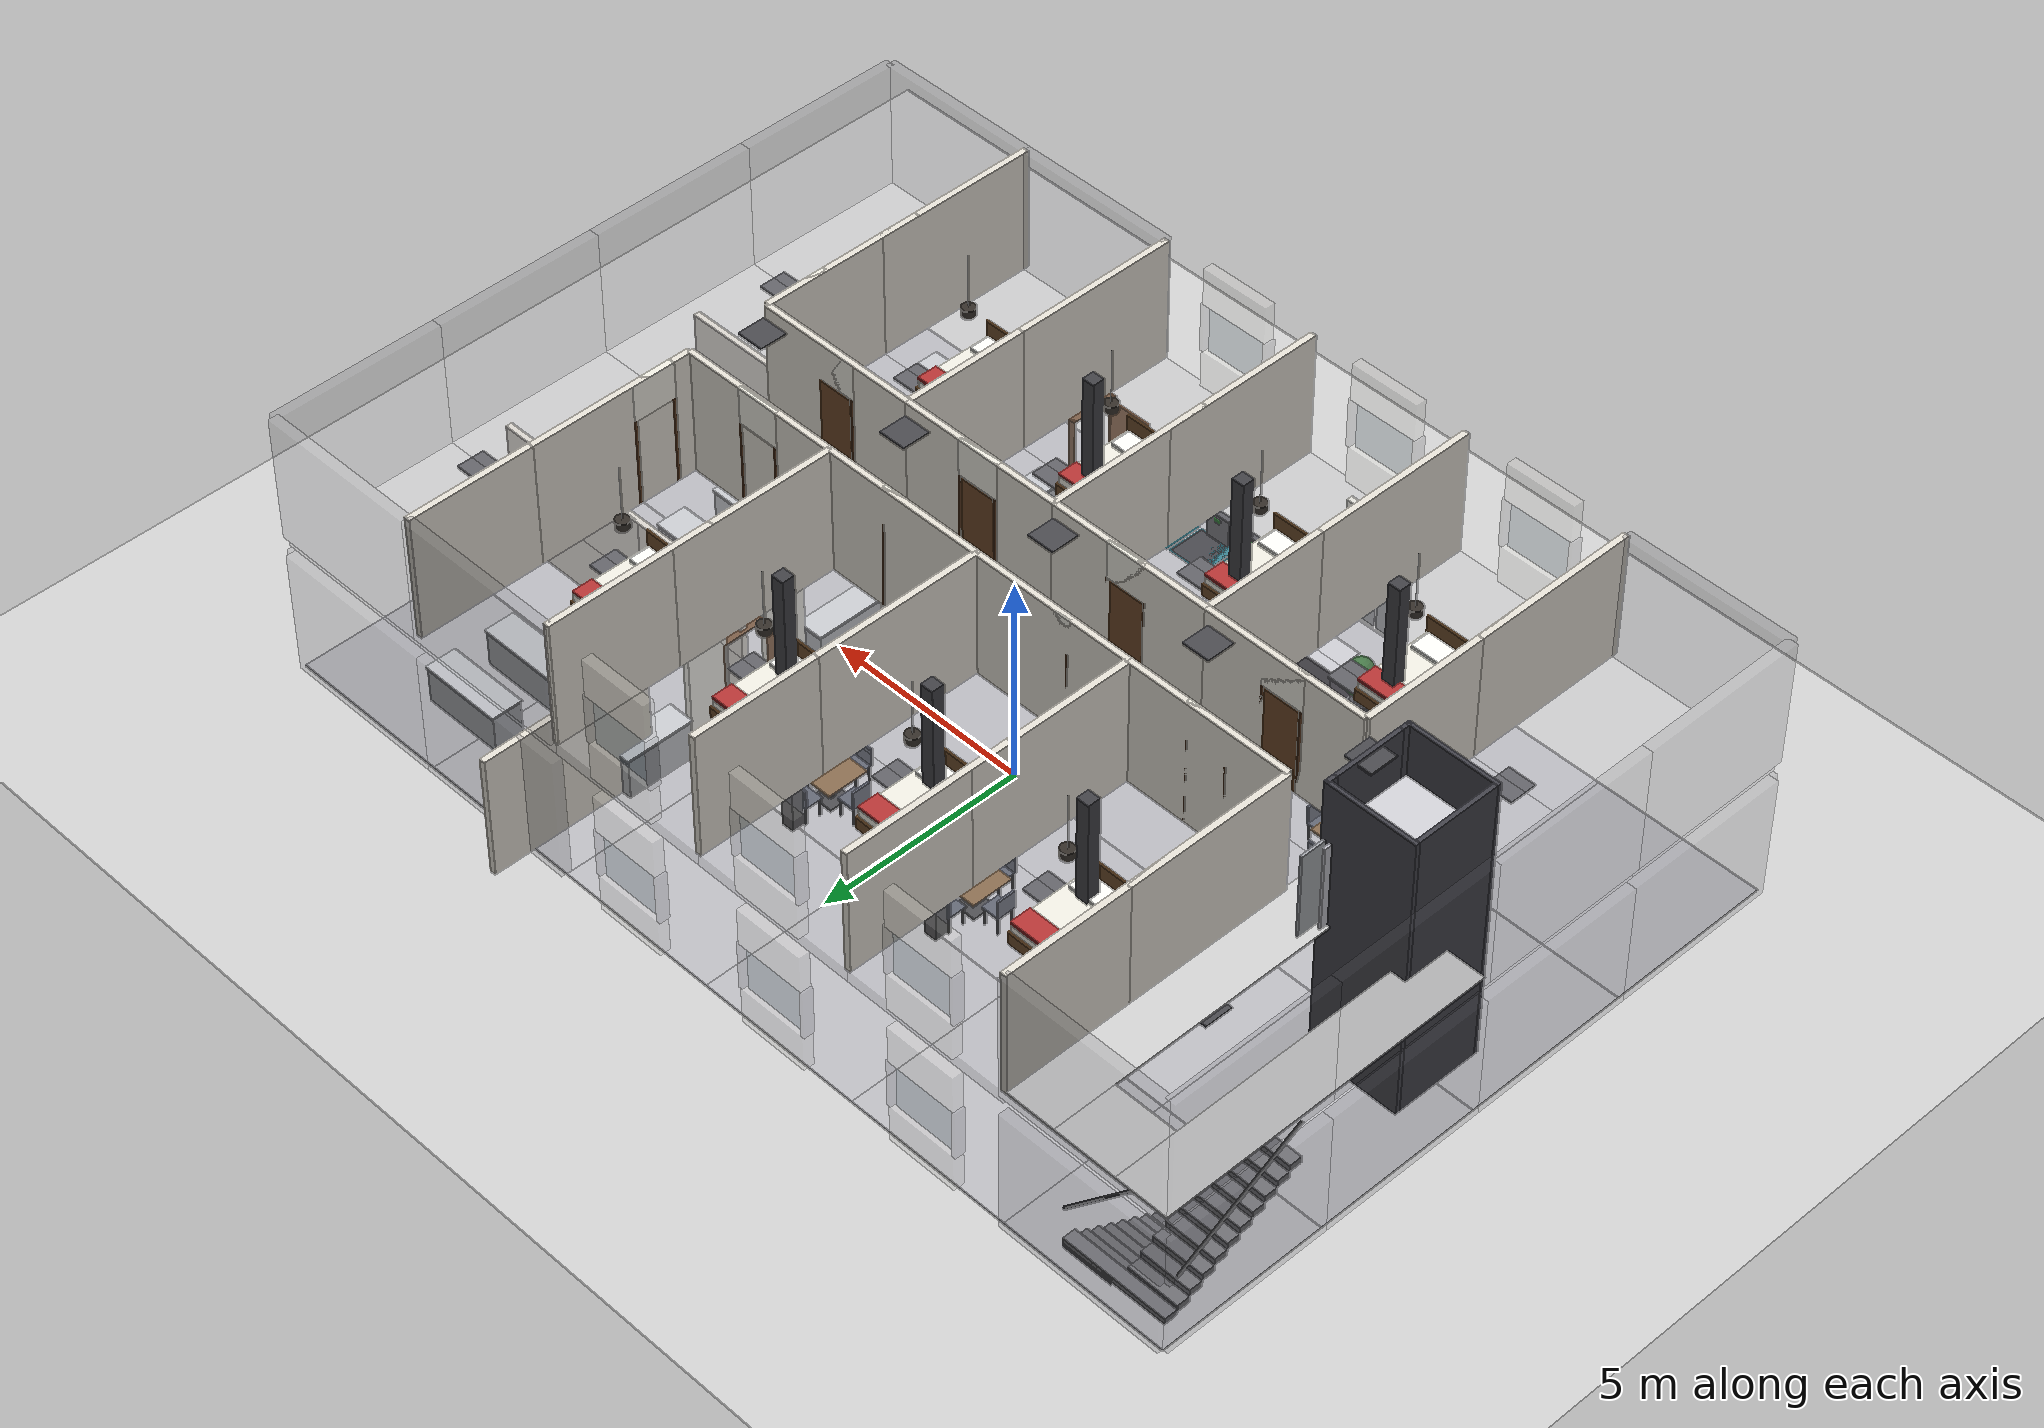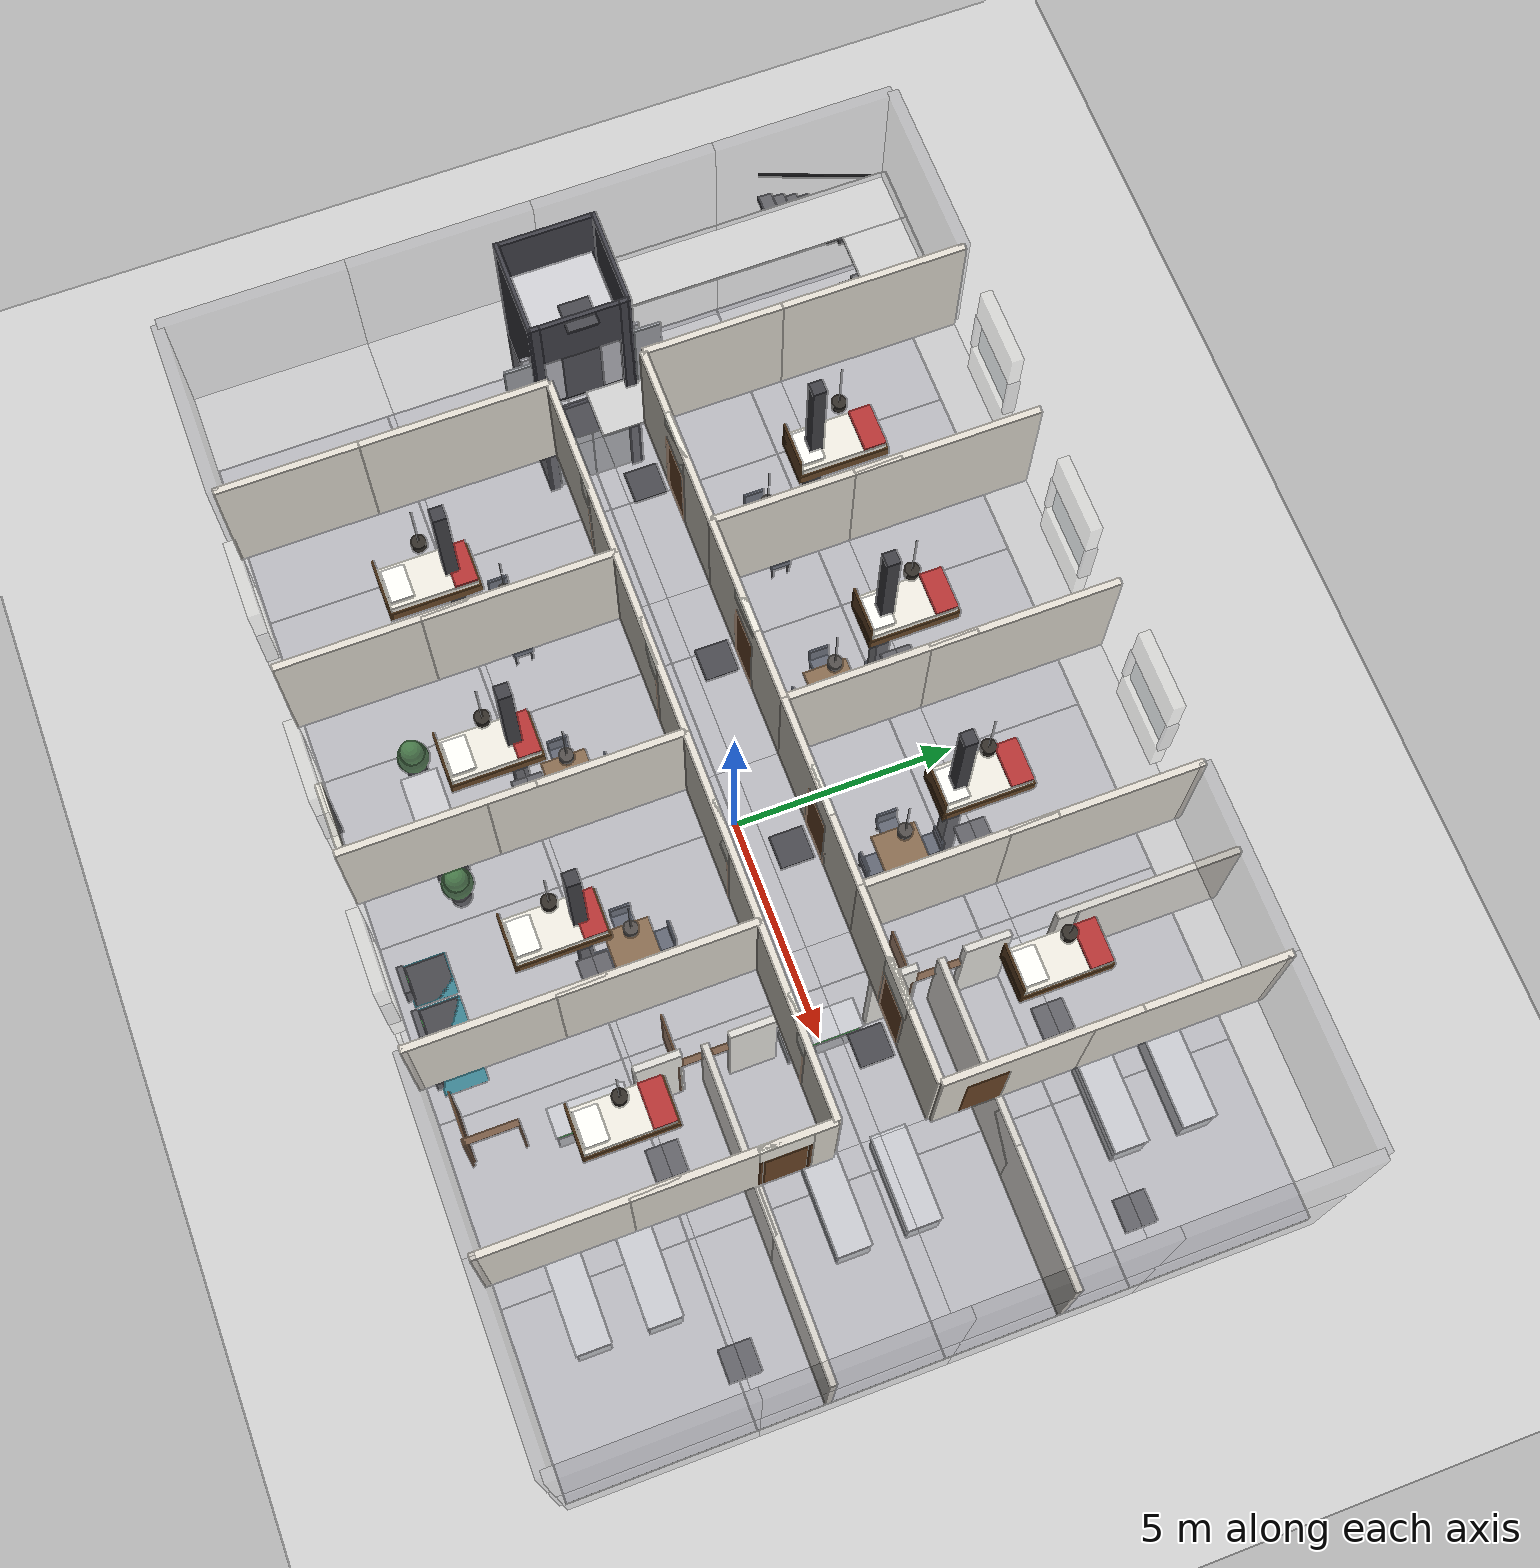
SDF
<?xml version="1.0" ?>
<sdf version="1.6">
  <world name="restaurant">
    <!-- A global light source -->
    <include>
      <uri>model://sun</uri>
    </include>
    <!-- A ground plane -->
    <include>
      <uri>model://ground_plane</uri>
    </include>

    <physics type="ode">
      <max_step_size>0.001</max_step_size>
      <real_time_factor>1</real_time_factor>
      <real_time_update_rate>1000</real_time_update_rate>
    </physics>

    <!-- Ground Floor Assembly -->
    <include>
      <name>ground_floor_inst</name>
      <uri>model://ground_floor</uri>
      <pose>0 0 0 0 0 0</pose>
    </include>

    <!-- First Floor Assembly -->
    <include>
      <name>first_floor_inst</name>
      <uri>model://first_floor</uri>
      <pose>0 0 3.5 0 0 0</pose>
    </include>

    <include>
      <name>lift_assembly_inst</name>
      <uri>model://_fixtures/lift_assembly</uri>
      <pose>-10 0 0 0 0 -1.5708</pose>
    </include>

  </world>
</sdf>

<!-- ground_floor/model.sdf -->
<sdf version="1.6">
  <model name="ground_floor">
    <static>true</static>

    <!-- Floor Slabs (6x4 grid) -->
    <!-- Row 1 (y = -6) -->
    <include><name>floor_slab_0_0</name><uri>model://_components/floor_slab</uri><pose>-10 -6 0 0 0 0</pose></include>
    <include><name>floor_slab_1_0</name><uri>model://_components/floor_slab</uri><pose>-6 -6 0 0 0 0</pose></include>
    <include><name>floor_slab_2_0</name><uri>model://_components/floor_slab</uri><pose>-2 -6 0 0 0 0</pose></include>
    <include><name>floor_slab_3_0</name><uri>model://_components/floor_slab</uri><pose>2 -6 0 0 0 0</pose></include>
    <include><name>floor_slab_4_0</name><uri>model://_components/floor_slab</uri><pose>6 -6 0 0 0 0</pose></include>
    <include><name>floor_slab_5_0</name><uri>model://_components/floor_slab</uri><pose>10 -6 0 0 0 0</pose></include>

    <!-- Row 2 (y = -2) -->
    <include><name>floor_slab_0_1</name><uri>model://_components/floor_slab</uri><pose>-10 -2 0 0 0 0</pose></include>
    <include><name>floor_slab_1_1</name><uri>model://_components/floor_slab</uri><pose>-6 -2 0 0 0 0</pose></include>
    <include><name>floor_slab_2_1</name><uri>model://_components/floor_slab</uri><pose>-2 -2 0 0 0 0</pose></include>
    <include><name>floor_slab_3_1</name><uri>model://_components/floor_slab</uri><pose>2 -2 0 0 0 0</pose></include>
    <include><name>floor_slab_4_1</name><uri>model://_components/floor_slab</uri><pose>6 -2 0 0 0 0</pose></include>
    <include><name>floor_slab_5_1</name><uri>model://_components/floor_slab</uri><pose>10 -2 0 0 0 0</pose></include>

    <!-- Row 3 (y = 2) -->
    <include><name>floor_slab_0_2</name><uri>model://_components/floor_slab</uri><pose>-10 2 0 0 0 0</pose></include>
    <include><name>floor_slab_1_2</name><uri>model://_components/floor_slab</uri><pose>-6 2 0 0 0 0</pose></include>
    <include><name>floor_slab_2_2</name><uri>model://_components/floor_slab</uri><pose>-2 2 0 0 0 0</pose></include>
    <include><name>floor_slab_3_2</name><uri>model://_components/floor_slab</uri><pose>2 2 0 0 0 0</pose></include>
    <include><name>floor_slab_4_2</name><uri>model://_components/floor_slab</uri><pose>6 2 0 0 0 0</pose></include>
    <include><name>floor_slab_5_2</name><uri>model://_components/floor_slab</uri><pose>10 2 0 0 0 0</pose></include>

    <!-- Row 4 (y = 6) -->
    <include><name>floor_slab_0_3</name><uri>model://_components/floor_slab</uri><pose>-10 6 0 0 0 0</pose></include>
    <include><name>floor_slab_1_3</name><uri>model://_components/floor_slab</uri><pose>-6 6 0 0 0 0</pose></include>
    <include><name>floor_slab_2_3</name><uri>model://_components/floor_slab</uri><pose>-2 6 0 0 0 0</pose></include>
    <include><name>floor_slab_3_3</name><uri>model://_components/floor_slab</uri><pose>2 6 0 0 0 0</pose></include>
    <include><name>floor_slab_4_3</name><uri>model://_components/floor_slab</uri><pose>6 6 0 0 0 0</pose></include>
    <include><name>floor_slab_5_3</name><uri>model://_components/floor_slab</uri><pose>10 6 0 0 0 0</pose></include>

    <!-- Exterior Walls -->
    <!-- South Facade (y = -8) -->
    <include><name>ext_wall_s0</name><uri>model://_components/wall_exterior</uri><pose>-10 -8 0 0 0 0</pose></include>
    <include><name>ext_wall_s1</name><uri>model://_components/window_standard</uri><pose>-6 -8 0 0 0 0</pose></include>
    <include><name>ext_wall_s2</name><uri>model://_components/door_double</uri><pose>-2 -8 0 0 0 0</pose></include>
    <include><name>ext_wall_s3</name><uri>model://_components/window_standard</uri><pose>2 -8 0 0 0 0</pose></include>
    <include><name>ext_wall_s4</name><uri>model://_components/wall_exterior</uri><pose>6 -8 0 0 0 0</pose></include>
    <include><name>ext_wall_s5</name><uri>model://_components/wall_exterior</uri><pose>10 -8 0 0 0 0</pose></include>

    <!-- North Facade (y = 8) -->
    <include><name>ext_wall_n0</name><uri>model://_components/wall_exterior</uri><pose>-10 8 0 0 0 3.14159</pose></include>
    <include><name>ext_wall_n1</name><uri>model://_components/window_standard</uri><pose>-6 8 0 0 0 3.14159</pose></include>
    <include><name>ext_wall_n2</name><uri>model://_components/window_standard</uri><pose>-2 8 0 0 0 3.14159</pose></include>
    <include><name>ext_wall_n3</name><uri>model://_components/window_standard</uri><pose>2 8 0 0 0 3.14159</pose></include>
    <include><name>ext_wall_n4</name><uri>model://_components/wall_exterior</uri><pose>6 8 0 0 0 3.14159</pose></include>
    <include><name>ext_wall_n5</name><uri>model://_components/wall_exterior</uri><pose>10 8 0 0 0 3.14159</pose></include>

    <!-- West Facade (x = -12) -->
    <include><name>ext_wall_w0</name><uri>model://_components/wall_exterior</uri><pose>-12 -6 0 0 0 1.5708</pose></include>
    <include><name>ext_wall_w1</name><uri>model://_components/wall_exterior</uri><pose>-12 -2 0 0 0 1.5708</pose></include>
    <include><name>ext_wall_w2</name><uri>model://_components/wall_exterior</uri><pose>-12 2 0 0 0 1.5708</pose></include>
    <include><name>ext_wall_w3</name><uri>model://_components/wall_exterior</uri><pose>-12 6 0 0 0 1.5708</pose></include>

    <!-- East Facade (x = 12) -->
    <include><name>ext_wall_e0</name><uri>model://_components/wall_exterior</uri><pose>12 -6 0 0 0 1.5708</pose></include>
    <include><name>ext_wall_e1</name><uri>model://_components/wall_exterior</uri><pose>12 -2 0 0 0 1.5708</pose></include>
    <include><name>ext_wall_e2</name><uri>model://_components/wall_exterior</uri><pose>12 2 0 0 0 1.5708</pose></include>
    <include><name>ext_wall_e3</name><uri>model://_components/wall_exterior</uri><pose>12 6 0 0 0 1.5708</pose></include>

    <!-- Pillars / Columns -->
    <include><name>column_0</name><uri>model://_components/column</uri><pose>-6 -4 0 0 0 0</pose></include>
    <include><name>column_1</name><uri>model://_components/column</uri><pose>-2 -4 0 0 0 0</pose></include>
    <include><name>column_2</name><uri>model://_components/column</uri><pose>2 -4 0 0 0 0</pose></include>
    <include><name>column_3</name><uri>model://_components/column</uri><pose>-6 4 0 0 0 0</pose></include>
    <include><name>column_4</name><uri>model://_components/column</uri><pose>-2 4 0 0 0 0</pose></include>
    <include><name>column_5</name><uri>model://_components/column</uri><pose>2 4 0 0 0 0</pose></include>

    <!-- Staircase (Back-Left Area) - moved to the former lift spot, same working rotation -->
    <include><name>stairs</name><uri>model://_fixtures/staircase</uri><pose>-10 5.5 0 0 0 1.5708</pose></include>

    <!-- Kitchen Partition Wall (x = 5.0) and Gaps for Counters / Doors -->
    <include><name>kitchen_partition_n</name><uri>model://_components/wall_segment_4m</uri><pose>5.0 7.0 0 0 0 1.5708</pose></include>
    <include><name>kitchen_partition_mid1</name><uri>model://_components/wall_segment</uri><pose>5.0 3.5 0 0 0 1.5708</pose></include>
    <include><name>kitchen_partition_mid2</name><uri>model://_components/wall_segment</uri><pose>5.0 1.5 0 0 0 1.5708</pose></include>
    <include><name>kitchen_partition_mid3</name><uri>model://_components/wall_segment</uri><pose>5.0 -1.5 0 0 0 1.5708</pose></include>
    <include><name>kitchen_partition_mid4</name><uri>model://_components/wall_segment</uri><pose>5.0 -3.5 0 0 0 1.5708</pose></include>

    <!-- Kitchen Side Walls (East-West division walls) -->
    <!-- Kitchen 1 vs Kitchen 2 (y = 2.5) -->
    <include><name>kitchen_wall_1_2_a</name><uri>model://_components/wall_segment_4m</uri><pose>7.0 2.5 0 0 0 0</pose></include>
    <include><name>kitchen_wall_1_2_b</name><uri>model://_components/wall_segment_4m</uri><pose>10.0 2.5 0 0 0 0</pose></include>
    <!-- Kitchen 2 vs Kitchen 3 (y = -2.5) -->
    <include><name>kitchen_wall_2_3_a</name><uri>model://_components/wall_segment_4m</uri><pose>7.0 -2.5 0 0 0 0</pose></include>
    <include><name>kitchen_wall_2_3_b</name><uri>model://_components/wall_segment_4m</uri><pose>10.0 -2.5 0 0 0 0</pose></include>

    <!-- Kitchen Entry Doors (placed in partition wall at x = 5.0) -->
    <include><name>kitchen_door_1</name><uri>model://_components/door_single_wide</uri><pose>5.0 2.5 0 0 0 1.5708</pose></include>
    <include><name>kitchen_door_2</name><uri>model://_components/door_single_wide</uri><pose>5.0 -2.5 0 0 0 1.5708</pose></include>
    <include><name>kitchen_door_3</name><uri>model://_components/door_single_wide</uri><pose>5.0 -7.0 0 0 0 1.5708</pose></include>

    <!-- Three Receiving Counters (Handoff area) -->
    <include><name>receiving_counter_1</name><uri>model://_furniture/receiving_counter</uri><pose>5.0 5.0 0 0 0 1.5708</pose></include>
    <include><name>receiving_counter_2</name><uri>model://_furniture/receiving_counter</uri><pose>5.0 0.0 0 0 0 1.5708</pose></include>
    <include><name>receiving_counter_3</name><uri>model://_furniture/receiving_counter</uri><pose>5.0 -5.0 0 0 0 1.5708</pose></include>

    <!-- Kitchen Internal Counters -->
    <!-- Kitchen 1 -->
    <include><name>k1_counter_1</name><uri>model://_furniture/kitchen_counter</uri><pose>8.5 5.0 0 0 0 0</pose></include>
    <include><name>k1_counter_2</name><uri>model://_furniture/kitchen_counter</uri><pose>8.5 6.5 0 0 0 0</pose></include>
    <!-- Kitchen 2 -->
    <include><name>k2_counter_1</name><uri>model://_furniture/kitchen_counter</uri><pose>8.5 0.5 0 0 0 0</pose></include>
    <include><name>k2_counter_2</name><uri>model://_furniture/kitchen_counter</uri><pose>8.5 -1.0 0 0 0 0</pose></include>
    <!-- Kitchen 3 -->
    <include><name>k3_counter_1</name><uri>model://_furniture/kitchen_counter</uri><pose>8.5 -5.0 0 0 0 0</pose></include>
    <include><name>k3_counter_2</name><uri>model://_furniture/kitchen_counter</uri><pose>8.5 -6.5 0 0 0 0</pose></include>

    <!-- Dining Hall: 6 Tables and 24 Chairs -->
    <!-- Table 1 (x = -6, y = 3) -->
    <include><name>table_1</name><uri>model://_furniture/dining_table_4</uri><pose>-6 3 0 0 0 0</pose></include>
    <include><name>table_1_chair_n</name><uri>model://_furniture/chair</uri><pose>-6 3.65 0 0 0 -1.5708</pose></include>
    <include><name>table_1_chair_s</name><uri>model://_furniture/chair</uri><pose>-6 2.35 0 0 0 1.5708</pose></include>
    <include><name>table_1_chair_e</name><uri>model://_furniture/chair</uri><pose>-5.35 3 0 0 0 3.14159</pose></include>
    <include><name>table_1_chair_w</name><uri>model://_furniture/chair</uri><pose>-6.65 3 0 0 0 0</pose></include>

    <!-- Table 2 (x = -6, y = -3) -->
    <include><name>table_2</name><uri>model://_furniture/dining_table_4</uri><pose>-6 -3 0 0 0 0</pose></include>
    <include><name>table_2_chair_n</name><uri>model://_furniture/chair</uri><pose>-6 -2.35 0 0 0 -1.5708</pose></include>
    <include><name>table_2_chair_s</name><uri>model://_furniture/chair</uri><pose>-6 -3.65 0 0 0 1.5708</pose></include>
    <include><name>table_2_chair_e</name><uri>model://_furniture/chair</uri><pose>-5.35 -3 0 0 0 3.14159</pose></include>
    <include><name>table_2_chair_w</name><uri>model://_furniture/chair</uri><pose>-6.65 -3 0 0 0 0</pose></include>

    <!-- Table 3 (x = -2, y = 3) -->
    <include><name>table_3</name><uri>model://_furniture/dining_table_4</uri><pose>-2 3 0 0 0 0</pose></include>
    <include><name>table_3_chair_n</name><uri>model://_furniture/chair</uri><pose>-2 3.65 0 0 0 -1.5708</pose></include>
    <include><name>table_3_chair_s</name><uri>model://_furniture/chair</uri><pose>-2 2.35 0 0 0 1.5708</pose></include>
    <include><name>table_3_chair_e</name><uri>model://_furniture/chair</uri><pose>-1.35 3 0 0 0 3.14159</pose></include>
    <include><name>table_3_chair_w</name><uri>model://_furniture/chair</uri><pose>-2.65 3 0 0 0 0</pose></include>

    <!-- Table 4 (x = -2, y = -3) -->
    <include><name>table_4</name><uri>model://_furniture/dining_table_4</uri><pose>-2 -3 0 0 0 0</pose></include>
    <include><name>table_4_chair_n</name><uri>model://_furniture/chair</uri><pose>-2 -2.35 0 0 0 -1.5708</pose></include>
    <include><name>table_4_chair_s</name><uri>model://_furniture/chair</uri><pose>-2 -3.65 0 0 0 1.5708</pose></include>
    <include><name>table_4_chair_e</name><uri>model://_furniture/chair</uri><pose>-1.35 -3 0 0 0 3.14159</pose></include>
    <include><name>table_4_chair_w</name><uri>model://_furniture/chair</uri><pose>-2.65 -3 0 0 0 0</pose></include>

    <!-- Table 5 (x = 2, y = 3) -->
    <include><name>table_5</name><uri>model://_furniture/dining_table_4</uri><pose>2 3 0 0 0 0</pose></include>
    <include><name>table_5_chair_n</name><uri>model://_furniture/chair</uri><pose>2 3.65 0 0 0 -1.5708</pose></include>
    <include><name>table_5_chair_s</name><uri>model://_furniture/chair</uri><pose>2 2.35 0 0 0 1.5708</pose></include>
    <include><name>table_5_chair_e</name><uri>model://_furniture/chair</uri><pose>2.65 3 0 0 0 3.14159</pose></include>
    <include><name>table_5_chair_w</name><uri>model://_furniture/chair</uri><pose>1.35 3 0 0 0 0</pose></include>

    <!-- Table 6 (x = 2, y = -3) -->
    <include><name>table_6</name><uri>model://_furniture/dining_table_4</uri><pose>2 -3 0 0 0 0</pose></include>
    <include><name>table_6_chair_n</name><uri>model://_furniture/chair</uri><pose>2 -2.35 0 0 0 -1.5708</pose></include>
    <include><name>table_6_chair_s</name><uri>model://_furniture/chair</uri><pose>2 -3.65 0 0 0 1.5708</pose></include>
    <include><name>table_6_chair_e</name><uri>model://_furniture/chair</uri><pose>2.65 -3 0 0 0 3.14159</pose></include>
    <include><name>table_6_chair_w</name><uri>model://_furniture/chair</uri><pose>1.35 -3 0 0 0 0</pose></include>

    <!-- Reception Area (near entrance) -->
    <include><name>reception_desk</name><uri>model://_furniture/reception_counter</uri><pose>-2 -6 0 0 0 3.14159</pose></include>
    <include><name>plant_lobby_l</name><uri>model://_furniture/indoor_plant</uri><pose>-3.5 -6 0 0 0 0</pose></include>
    <include><name>plant_lobby_r</name><uri>model://_furniture/indoor_plant</uri><pose>-0.5 -6 0 0 0 0</pose></include>

    <!-- Charging Station Area (near kitchens / service pathway) -->
    <include><name>dock_1</name><uri>model://_furniture/charging_dock</uri><pose>1.0 -7.2 0 0 0 1.5708</pose></include>
    <include><name>dock_2</name><uri>model://_furniture/charging_dock</uri><pose>2.0 -7.2 0 0 0 1.5708</pose></include>
    <include><name>dock_3</name><uri>model://_furniture/charging_dock</uri><pose>3.0 -7.2 0 0 0 1.5708</pose></include>

    <!-- Ceiling Lights (arranged on ceiling grid at z = 3.4m) -->
    <include><name>light_c0_0</name><uri>model://_lighting/ceiling_light_panel</uri><pose>-9 -4 3.4 0 0 0</pose></include>
    <include><name>light_c1_0</name><uri>model://_lighting/ceiling_light_panel</uri><pose>-5 -4 3.4 0 0 0</pose></include>
    <include><name>light_c2_0</name><uri>model://_lighting/ceiling_light_panel</uri><pose>-1 -4 3.4 0 0 0</pose></include>
    <include><name>light_c3_0</name><uri>model://_lighting/ceiling_light_panel</uri><pose>3 -4 3.4 0 0 0</pose></include>
    <include><name>light_c4_0</name><uri>model://_lighting/ceiling_light_panel</uri><pose>7 -4 3.4 0 0 0</pose></include>
    <include><name>light_c5_0</name><uri>model://_lighting/ceiling_light_panel</uri><pose>11 -4 3.4 0 0 0</pose></include>

    <include><name>light_c0_1</name><uri>model://_lighting/ceiling_light_panel</uri><pose>-9 4 3.4 0 0 0</pose></include>
    <include><name>light_c1_1</name><uri>model://_lighting/ceiling_light_panel</uri><pose>-5 4 3.4 0 0 0</pose></include>
    <include><name>light_c2_1</name><uri>model://_lighting/ceiling_light_panel</uri><pose>-1 4 3.4 0 0 0</pose></include>
    <include><name>light_c3_1</name><uri>model://_lighting/ceiling_light_panel</uri><pose>3 4 3.4 0 0 0</pose></include>
    <include><name>light_c4_1</name><uri>model://_lighting/ceiling_light_panel</uri><pose>7 4 3.4 0 0 0</pose></include>
    <include><name>light_c5_1</name><uri>model://_lighting/ceiling_light_panel</uri><pose>11 4 3.4 0 0 0</pose></include>

    <!-- Elegant Pendant Lights over Dining Tables -->
    <include><name>pendant_light_1</name><uri>model://_lighting/pendant_light</uri><pose>-6 3 3.4 0 0 0</pose></include>
    <include><name>pendant_light_2</name><uri>model://_lighting/pendant_light</uri><pose>-6 -3 3.4 0 0 0</pose></include>
    <include><name>pendant_light_3</name><uri>model://_lighting/pendant_light</uri><pose>-2 3 3.4 0 0 0</pose></include>
    <include><name>pendant_light_4</name><uri>model://_lighting/pendant_light</uri><pose>-2 -3 3.4 0 0 0</pose></include>
    <include><name>pendant_light_5</name><uri>model://_lighting/pendant_light</uri><pose>2 3 3.4 0 0 0</pose></include>
    <include><name>pendant_light_6</name><uri>model://_lighting/pendant_light</uri><pose>2 -3 3.4 0 0 0</pose></include>

  </model>
</sdf>

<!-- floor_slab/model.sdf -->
<sdf version="1.6">
  <model name="floor_slab">
    <static>true</static>
    <link name="floor_link">
      <pose>0 0 -0.15 0 0 0</pose>
      <collision name="floor_col">
        <geometry><box><size>4.0 4.0 0.30</size></box></geometry>
        <surface>
          <friction><ode><mu>0.9</mu><mu2>0.9</mu2></ode></friction>
        </surface>
      </collision>
      <visual name="floor_vis">
        <geometry><box><size>4.0 4.0 0.30</size></box></geometry>
        <material>
          <!-- Polished porcelain: light grey, strong specular sheen -->
          <ambient>0.55 0.55 0.57 1</ambient>
          <diffuse>0.72 0.72 0.74 1</diffuse>
          <specular>0.55 0.55 0.57 1</specular>
          <emissive>0 0 0 1</emissive>
        </material>
      </visual>
    </link>
  </model>
</sdf>

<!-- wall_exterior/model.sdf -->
<sdf version="1.6">
  <model name="wall_exterior">
    <static>true</static>
    <link name="link">
      <pose>0 0 1.5 0 0 0</pose>
      <collision name="collision">
        <geometry>
          <box>
            <size>4.0 0.25 3.0</size>
          </box>
        </geometry>
      </collision>
      <visual name="visual">
        <geometry>
          <box>
            <size>4.0 0.25 3.0</size>
          </box>
        </geometry>
        <material>
          <ambient>0.35 0.35 0.38 1</ambient>
          <diffuse>0.35 0.35 0.38 1</diffuse>
          <specular>0.2 0.2 0.2 1</specular>
        </material>
        <transparency>0.85</transparency>
      </visual>
    </link>
  </model>
</sdf>

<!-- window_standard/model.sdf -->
<sdf version="1.6">
  <model name="window_standard">
    <static>true</static>
    <link name="frame_link">
      <!-- Sill (below glass) fill: z 0.0 -> 0.9 -->
      <collision name="sill_col">
        <pose>0 0 0.45 0 0 0</pose>
        <geometry><box><size>1.7 0.25 0.9</size></box></geometry>
      </collision>
      <visual name="sill_vis">
        <pose>0 0 0.45 0 0 0</pose>
        <geometry><box><size>1.7 0.25 0.9</size></box></geometry>
        <material><ambient>0.85 0.84 0.80 1</ambient><diffuse>0.92 0.91 0.87 1</diffuse><specular>0.05 0.05 0.05 1</specular></material>
        <transparency>0.85</transparency>
      </visual>

      <!-- Header (above glass): z 2.1 -> 3.0 -->
      <collision name="header_col">
        <pose>0 0 2.55 0 0 0</pose>
        <geometry><box><size>1.7 0.25 0.9</size></box></geometry>
      </collision>
      <visual name="header_vis">
        <pose>0 0 2.55 0 0 0</pose>
        <geometry><box><size>1.7 0.25 0.9</size></box></geometry>
        <material><ambient>0.85 0.84 0.80 1</ambient><diffuse>0.92 0.91 0.87 1</diffuse><specular>0.05 0.05 0.05 1</specular></material>
        <transparency>0.85</transparency>
      </visual>

      <!-- Left mullion -->
      <collision name="mull_left_col">
        <pose>-0.85 0 1.5 0 0 0</pose>
        <geometry><box><size>0.10 0.25 1.2</size></box></geometry>
      </collision>
      <visual name="mull_left_vis">
        <pose>-0.85 0 1.5 0 0 0</pose>
        <geometry><box><size>0.10 0.25 1.2</size></box></geometry>
        <material><ambient>0.30 0.30 0.32 1</ambient><diffuse>0.38 0.38 0.40 1</diffuse><specular>0.25 0.25 0.27 1</specular></material>
        <transparency>0.85</transparency>
      </visual>
      <!-- Right mullion -->
      <collision name="mull_right_col">
        <pose>0.85 0 1.5 0 0 0</pose>
        <geometry><box><size>0.10 0.25 1.2</size></box></geometry>
      </collision>
      <visual name="mull_right_vis">
        <pose>0.85 0 1.5 0 0 0</pose>
        <geometry><box><size>0.10 0.25 1.2</size></box></geometry>
        <material><ambient>0.30 0.30 0.32 1</ambient><diffuse>0.38 0.38 0.40 1</diffuse><specular>0.25 0.25 0.27 1</specular></material>
        <transparency>0.85</transparency>
      </visual>
    </link>

    <!-- ===== GLASS (visual only) ===== -->
    <link name="glass_link">
      <pose>0 0 1.5 0 0 0</pose>
      <visual name="glass_vis">
        <geometry><box><size>1.5 0.03 1.2</size></box></geometry>
        <material>
          <!-- Cool tinted transparent glass -->
          <ambient>0.35 0.45 0.50 0.30</ambient>
          <diffuse>0.45 0.55 0.60 0.30</diffuse>
          <specular>0.70 0.70 0.72 0.30</specular>
        </material>
        <transparency>0.7</transparency>
      </visual>
    </link>
  </model>
</sdf>

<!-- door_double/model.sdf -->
<sdf version="1.6">
  <model name="door_double">
    <static>true</static>
    <link name="frame_link">
      <collision name="jamb_left_col">
        <pose>-0.79 0 1.05 0 0 0</pose>
        <geometry><box><size>0.08 0.15 2.1</size></box></geometry>
      </collision>
      <visual name="jamb_left_vis">
        <pose>-0.79 0 1.05 0 0 0</pose>
        <geometry><box><size>0.08 0.15 2.1</size></box></geometry>
        <material><ambient>0.20 0.20 0.22 1</ambient><diffuse>0.28 0.28 0.30 1</diffuse><specular>0.30 0.30 0.32 1</specular></material>
      </visual>
      <collision name="jamb_right_col">
        <pose>0.79 0 1.05 0 0 0</pose>
        <geometry><box><size>0.08 0.15 2.1</size></box></geometry>
      </collision>
      <visual name="jamb_right_vis">
        <pose>0.79 0 1.05 0 0 0</pose>
        <geometry><box><size>0.08 0.15 2.1</size></box></geometry>
        <material><ambient>0.20 0.20 0.22 1</ambient><diffuse>0.28 0.28 0.30 1</diffuse><specular>0.30 0.30 0.32 1</specular></material>
      </visual>
      <collision name="head_col">
        <pose>0 0 2.55 0 0 0</pose>
        <geometry><box><size>1.66 0.15 0.9</size></box></geometry>
      </collision>
      <visual name="head_vis">
        <pose>0 0 2.55 0 0 0</pose>
        <geometry><box><size>1.66 0.15 0.9</size></box></geometry>
        <material><ambient>0.85 0.84 0.80 1</ambient><diffuse>0.92 0.91 0.87 1</diffuse><specular>0.05 0.05 0.05 1</specular></material>
      </visual>
    </link>

    <link name="leaf_left">
      <pose>-0.375 -0.06 1.05 0 0 0</pose>
      <collision name="col"><geometry><box><size>0.70 0.04 2.05</size></box></geometry></collision>
      <visual name="vis">
        <geometry><box><size>0.70 0.04 2.05</size></box></geometry>
        <!-- Brushed-metal look via high specular -->
        <material><ambient>0.55 0.56 0.58 1</ambient><diffuse>0.65 0.66 0.68 1</diffuse><specular>0.60 0.60 0.62 1</specular></material>
      </visual>
    </link>
    <link name="leaf_right">
      <pose>0.375 -0.06 1.05 0 0 0</pose>
      <collision name="col"><geometry><box><size>0.70 0.04 2.05</size></box></geometry></collision>
      <visual name="vis">
        <geometry><box><size>0.70 0.04 2.05</size></box></geometry>
        <material><ambient>0.55 0.56 0.58 1</ambient><diffuse>0.65 0.66 0.68 1</diffuse><specular>0.60 0.60 0.62 1</specular></material>
      </visual>
    </link>
  </model>
</sdf>

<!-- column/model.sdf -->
<!--
  column | Module A - Structural Components
  0.30 x 0.30 m footprint, 3.0 m tall. Bottom at z=0. Origin at footprint centre, floor level.
-->
<sdf version="1.6">
  <model name="column">
    <static>true</static>
    <link name="column_link">
      <pose>0 0 1.5 0 0 0</pose>
      <collision name="column_col">
        <geometry><box><size>0.30 0.30 3.0</size></box></geometry>
      </collision>
      <visual name="column_vis">
        <geometry><box><size>0.30 0.30 3.0</size></box></geometry>
        <material>
          <!-- Premium charcoal cladding -->
          <ambient>0.18 0.18 0.20 1</ambient>
          <diffuse>0.25 0.25 0.27 1</diffuse>
          <specular>0.30 0.30 0.32 1</specular>
        </material>
      </visual>
    </link>
  </model>
</sdf>

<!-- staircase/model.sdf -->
<sdf version="1.6">
  <model name="staircase">
    <static>true</static>

    <!-- ===================== FLIGHT A (steps 1..10, +X, Y 0..1.2) ===================== -->
    <link name="flight_a">
      <!-- Step template repeated; tread 0.30, rise 0.165, top of step n at n*0.165 -->
      <!-- Step 1 -->
      <collision name="a1_col"><pose>0.15 0.6 0.0825 0 0 0</pose><geometry><box><size>0.30 1.2 0.165</size></box></geometry></collision>
      <visual name="a1_vis"><pose>0.15 0.6 0.0825 0 0 0</pose><geometry><box><size>0.30 1.2 0.165</size></box></geometry>
        <material><ambient>0.30 0.30 0.32 1</ambient><diffuse>0.42 0.42 0.44 1</diffuse><specular>0.30 0.30 0.32 1</specular></material></visual>
      <!-- Step 2 -->
      <collision name="a2_col"><pose>0.45 0.6 0.2475 0 0 0</pose><geometry><box><size>0.30 1.2 0.165</size></box></geometry></collision>
      <visual name="a2_vis"><pose>0.45 0.6 0.2475 0 0 0</pose><geometry><box><size>0.30 1.2 0.165</size></box></geometry>
        <material><ambient>0.30 0.30 0.32 1</ambient><diffuse>0.42 0.42 0.44 1</diffuse><specular>0.30 0.30 0.32 1</specular></material></visual>
      <!-- Step 3 -->
      <collision name="a3_col"><pose>0.75 0.6 0.4125 0 0 0</pose><geometry><box><size>0.30 1.2 0.165</size></box></geometry></collision>
      <visual name="a3_vis"><pose>0.75 0.6 0.4125 0 0 0</pose><geometry><box><size>0.30 1.2 0.165</size></box></geometry>
        <material><ambient>0.30 0.30 0.32 1</ambient><diffuse>0.42 0.42 0.44 1</diffuse><specular>0.30 0.30 0.32 1</specular></material></visual>
      <!-- Step 4 -->
      <collision name="a4_col"><pose>1.05 0.6 0.5775 0 0 0</pose><geometry><box><size>0.30 1.2 0.165</size></box></geometry></collision>
      <visual name="a4_vis"><pose>1.05 0.6 0.5775 0 0 0</pose><geometry><box><size>0.30 1.2 0.165</size></box></geometry>
        <material><ambient>0.30 0.30 0.32 1</ambient><diffuse>0.42 0.42 0.44 1</diffuse><specular>0.30 0.30 0.32 1</specular></material></visual>
      <!-- Step 5 -->
      <collision name="a5_col"><pose>1.35 0.6 0.7425 0 0 0</pose><geometry><box><size>0.30 1.2 0.165</size></box></geometry></collision>
      <visual name="a5_vis"><pose>1.35 0.6 0.7425 0 0 0</pose><geometry><box><size>0.30 1.2 0.165</size></box></geometry>
        <material><ambient>0.30 0.30 0.32 1</ambient><diffuse>0.42 0.42 0.44 1</diffuse><specular>0.30 0.30 0.32 1</specular></material></visual>
      <!-- Step 6 -->
      <collision name="a6_col"><pose>1.65 0.6 0.9075 0 0 0</pose><geometry><box><size>0.30 1.2 0.165</size></box></geometry></collision>
      <visual name="a6_vis"><pose>1.65 0.6 0.9075 0 0 0</pose><geometry><box><size>0.30 1.2 0.165</size></box></geometry>
        <material><ambient>0.30 0.30 0.32 1</ambient><diffuse>0.42 0.42 0.44 1</diffuse><specular>0.30 0.30 0.32 1</specular></material></visual>
      <!-- Step 7 -->
      <collision name="a7_col"><pose>1.95 0.6 1.0725 0 0 0</pose><geometry><box><size>0.30 1.2 0.165</size></box></geometry></collision>
      <visual name="a7_vis"><pose>1.95 0.6 1.0725 0 0 0</pose><geometry><box><size>0.30 1.2 0.165</size></box></geometry>
        <material><ambient>0.30 0.30 0.32 1</ambient><diffuse>0.42 0.42 0.44 1</diffuse><specular>0.30 0.30 0.32 1</specular></material></visual>
      <!-- Step 8 -->
      <collision name="a8_col"><pose>2.25 0.6 1.2375 0 0 0</pose><geometry><box><size>0.30 1.2 0.165</size></box></geometry></collision>
      <visual name="a8_vis"><pose>2.25 0.6 1.2375 0 0 0</pose><geometry><box><size>0.30 1.2 0.165</size></box></geometry>
        <material><ambient>0.30 0.30 0.32 1</ambient><diffuse>0.42 0.42 0.44 1</diffuse><specular>0.30 0.30 0.32 1</specular></material></visual>
      <!-- Step 9 -->
      <collision name="a9_col"><pose>2.55 0.6 1.4025 0 0 0</pose><geometry><box><size>0.30 1.2 0.165</size></box></geometry></collision>
      <visual name="a9_vis"><pose>2.55 0.6 1.4025 0 0 0</pose><geometry><box><size>0.30 1.2 0.165</size></box></geometry>
        <material><ambient>0.30 0.30 0.32 1</ambient><diffuse>0.42 0.42 0.44 1</diffuse><specular>0.30 0.30 0.32 1</specular></material></visual>
      <!-- Step 10 -->
      <collision name="a10_col"><pose>2.85 0.6 1.5675 0 0 0</pose><geometry><box><size>0.30 1.2 0.165</size></box></geometry></collision>
      <visual name="a10_vis"><pose>2.85 0.6 1.5675 0 0 0</pose><geometry><box><size>0.30 1.2 0.165</size></box></geometry>
        <material><ambient>0.30 0.30 0.32 1</ambient><diffuse>0.42 0.42 0.44 1</diffuse><specular>0.30 0.30 0.32 1</specular></material></visual>
    </link>

    <!-- ===================== LANDING (at z=1.65, X 2.7..3.0, Y 0..2.5) ===================== -->
    <link name="landing">
      <collision name="landing_col"><pose>2.85 1.25 1.6425 0 0 0</pose><geometry><box><size>0.30 2.5 0.15</size></box></geometry></collision>
      <visual name="landing_vis"><pose>2.85 1.25 1.6425 0 0 0</pose><geometry><box><size>0.30 2.5 0.15</size></box></geometry>
        <material><ambient>0.28 0.28 0.30 1</ambient><diffuse>0.40 0.40 0.42 1</diffuse><specular>0.35 0.35 0.37 1</specular></material></visual>
    </link>

    <!-- ===================== FLIGHT B (steps 11..20, -X, Y 1.3..2.5) ===================== -->
    <link name="flight_b">
      <!-- Step 11 (first above landing 1.65) -->
      <collision name="b11_col"><pose>2.55 1.9 1.7325 0 0 0</pose><geometry><box><size>0.30 1.2 0.165</size></box></geometry></collision>
      <visual name="b11_vis"><pose>2.55 1.9 1.7325 0 0 0</pose><geometry><box><size>0.30 1.2 0.165</size></box></geometry>
        <material><ambient>0.30 0.30 0.32 1</ambient><diffuse>0.42 0.42 0.44 1</diffuse><specular>0.30 0.30 0.32 1</specular></material></visual>
      <collision name="b12_col"><pose>2.25 1.9 1.8975 0 0 0</pose><geometry><box><size>0.30 1.2 0.165</size></box></geometry></collision>
      <visual name="b12_vis"><pose>2.25 1.9 1.8975 0 0 0</pose><geometry><box><size>0.30 1.2 0.165</size></box></geometry>
        <material><ambient>0.30 0.30 0.32 1</ambient><diffuse>0.42 0.42 0.44 1</diffuse><specular>0.30 0.30 0.32 1</specular></material></visual>
      <collision name="b13_col"><pose>1.95 1.9 2.0625 0 0 0</pose><geometry><box><size>0.30 1.2 0.165</size></box></geometry></collision>
      <visual name="b13_vis"><pose>1.95 1.9 2.0625 0 0 0</pose><geometry><box><size>0.30 1.2 0.165</size></box></geometry>
        <material><ambient>0.30 0.30 0.32 1</ambient><diffuse>0.42 0.42 0.44 1</diffuse><specular>0.30 0.30 0.32 1</specular></material></visual>
      <collision name="b14_col"><pose>1.65 1.9 2.2275 0 0 0</pose><geometry><box><size>0.30 1.2 0.165</size></box></geometry></collision>
      <visual name="b14_vis"><pose>1.65 1.9 2.2275 0 0 0</pose><geometry><box><size>0.30 1.2 0.165</size></box></geometry>
        <material><ambient>0.30 0.30 0.32 1</ambient><diffuse>0.42 0.42 0.44 1</diffuse><specular>0.30 0.30 0.32 1</specular></material></visual>
      <collision name="b15_col"><pose>1.35 1.9 2.3925 0 0 0</pose><geometry><box><size>0.30 1.2 0.165</size></box></geometry></collision>
      <visual name="b15_vis"><pose>1.35 1.9 2.3925 0 0 0</pose><geometry><box><size>0.30 1.2 0.165</size></box></geometry>
        <material><ambient>0.30 0.30 0.32 1</ambient><diffuse>0.42 0.42 0.44 1</diffuse><specular>0.30 0.30 0.32 1</specular></material></visual>
      <collision name="b16_col"><pose>1.05 1.9 2.5575 0 0 0</pose><geometry><box><size>0.30 1.2 0.165</size></box></geometry></collision>
      <visual name="b16_vis"><pose>1.05 1.9 2.5575 0 0 0</pose><geometry><box><size>0.30 1.2 0.165</size></box></geometry>
        <material><ambient>0.30 0.30 0.32 1</ambient><diffuse>0.42 0.42 0.44 1</diffuse><specular>0.30 0.30 0.32 1</specular></material></visual>
      <collision name="b17_col"><pose>0.75 1.9 2.7225 0 0 0</pose><geometry><box><size>0.30 1.2 0.165</size></box></geometry></collision>
      <visual name="b17_vis"><pose>0.75 1.9 2.7225 0 0 0</pose><geometry><box><size>0.30 1.2 0.165</size></box></geometry>
        <material><ambient>0.30 0.30 0.32 1</ambient><diffuse>0.42 0.42 0.44 1</diffuse><specular>0.30 0.30 0.32 1</specular></material></visual>
      <collision name="b18_col"><pose>0.45 1.9 2.8875 0 0 0</pose><geometry><box><size>0.30 1.2 0.165</size></box></geometry></collision>
      <visual name="b18_vis"><pose>0.45 1.9 2.8875 0 0 0</pose><geometry><box><size>0.30 1.2 0.165</size></box></geometry>
        <material><ambient>0.30 0.30 0.32 1</ambient><diffuse>0.42 0.42 0.44 1</diffuse><specular>0.30 0.30 0.32 1</specular></material></visual>
      <collision name="b19_col"><pose>0.15 1.9 3.0525 0 0 0</pose><geometry><box><size>0.30 1.2 0.165</size></box></geometry></collision>
      <visual name="b19_vis"><pose>0.15 1.9 3.0525 0 0 0</pose><geometry><box><size>0.30 1.2 0.165</size></box></geometry>
        <material><ambient>0.30 0.30 0.32 1</ambient><diffuse>0.42 0.42 0.44 1</diffuse><specular>0.30 0.30 0.32 1</specular></material></visual>
      <!-- 20 (top, reaches 3.30) -->
      <collision name="b20_col"><pose>-0.15 1.9 3.2175 0 0 0</pose><geometry><box><size>0.30 1.2 0.165</size></box></geometry></collision>
      <visual name="b20_vis"><pose>-0.15 1.9 3.2175 0 0 0</pose><geometry><box><size>0.30 1.2 0.165</size></box></geometry>
        <material><ambient>0.30 0.30 0.32 1</ambient><diffuse>0.42 0.42 0.44 1</diffuse><specular>0.30 0.30 0.32 1</specular></material></visual>
    </link>

    <!-- ===================== HANDRAIL (visual only, both flights outer edge) ===================== -->
    <link name="handrail">
      <!-- Flight A outer rail (Y=0.02), rising: walking line runs (0,0)->(3.0,1.65),
           rail offset +0.9m vertically above the pitch line, centered on the run -->
      <visual name="rail_a_vis"><pose>1.5 0.03 1.725 0 -0.5 0</pose>
        <geometry><box><size>3.4 0.05 0.05</size></box></geometry>
        <material><ambient>0.10 0.10 0.11 1</ambient><diffuse>0.16 0.16 0.17 1</diffuse><specular>0.40 0.40 0.42 1</specular></material></visual>
      <!-- Flight B outer rail (Y=2.48), rising the other way: walking line runs
           (2.7,1.65)->(-0.3,3.30), rail offset +0.9m vertically above the pitch line -->
      <visual name="rail_b_vis"><pose>1.2 2.47 3.375 0 0.5 0</pose>
        <geometry><box><size>3.4 0.05 0.05</size></box></geometry>
        <material><ambient>0.10 0.10 0.11 1</ambient><diffuse>0.16 0.16 0.17 1</diffuse><specular>0.40 0.40 0.42 1</specular></material></visual>
    </link>
  </model>
</sdf>

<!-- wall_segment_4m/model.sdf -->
<sdf version="1.6">
  <model name="wall_segment_4m">
    <static>true</static>
    <link name="link">
      <pose>0 0 1.5 0 0 0</pose>
      <collision name="collision">
        <geometry>
          <box>
            <size>4.0 0.15 3.0</size>
          </box>
        </geometry>
      </collision>
      <visual name="visual">
        <geometry>
          <box>
            <size>4.0 0.15 3.0</size>
          </box>
        </geometry>
        <material>
          <ambient>0.88 0.86 0.82 1</ambient>
          <diffuse>0.88 0.86 0.82 1</diffuse>
          <specular>0.1 0.1 0.1 1</specular>
        </material>
      </visual>
    </link>
  </model>
</sdf>

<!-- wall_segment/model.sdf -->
<sdf version="1.6">
  <model name="wall_segment">
    <static>true</static>

    <link name="wall_link">
      <!-- Lift the box so its bottom sits on the floor (half of 3.0 m). -->
      <pose>0 0 1.5 0 0 0</pose>

      <collision name="wall_collision">
        <geometry>
          <box>
            <size>1.0 0.15 3.0</size>
          </box>
        </geometry>
        <surface>
          <contact>
            <ode>
              <kp>1e7</kp>
              <kd>1.0</kd>
            </ode>
          </contact>
          <friction>
            <ode>
              <mu>0.8</mu>
              <mu2>0.8</mu2>
            </ode>
          </friction>
        </surface>
      </collision>

      <visual name="wall_visual">
        <geometry>
          <box>
            <size>1.0 0.15 3.0</size>
          </box>
        </geometry>
        <material>
          <!-- Premium warm off-white matte plaster -->
          <ambient>0.85 0.84 0.80 1</ambient>
          <diffuse>0.92 0.91 0.87 1</diffuse>
          <specular>0.05 0.05 0.05 1</specular>
          <emissive>0 0 0 1</emissive>
        </material>
      </visual>
    </link>
  </model>
</sdf>

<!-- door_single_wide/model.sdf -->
<sdf version="1.6">
  <model name="door_single_wide">
    <static>true</static>
    <link name="frame">
      <pose>0 0 0 0 0 0</pose>
      <!-- Left Post -->
      <collision name="left_post_collision">
        <pose>-0.575 0 1.05 0 0 0</pose>
        <geometry><box><size>0.05 0.15 2.1</size></box></geometry>
      </collision>
      <visual name="left_post_visual">
        <pose>-0.575 0 1.05 0 0 0</pose>
        <geometry><box><size>0.05 0.15 2.1</size></box></geometry>
        <material>
          <ambient>0.4 0.25 0.13 1</ambient>
          <diffuse>0.4 0.25 0.13 1</diffuse>
        </material>
      </visual>
      <!-- Right Post -->
      <collision name="right_post_collision">
        <pose>0.575 0 1.05 0 0 0</pose>
        <geometry><box><size>0.05 0.15 2.1</size></box></geometry>
      </collision>
      <visual name="right_post_visual">
        <pose>0.575 0 1.05 0 0 0</pose>
        <geometry><box><size>0.05 0.15 2.1</size></box></geometry>
        <material>
          <ambient>0.4 0.25 0.13 1</ambient>
          <diffuse>0.4 0.25 0.13 1</diffuse>
        </material>
      </visual>
      <!-- Header -->
      <collision name="header_collision">
        <pose>0 0 2.075 0 0 0</pose>
        <geometry><box><size>1.2 0.15 0.05</size></box></geometry>
      </collision>
      <visual name="header_visual">
        <pose>0 0 2.075 0 0 0</pose>
        <geometry><box><size>1.2 0.15 0.05</size></box></geometry>
        <material>
          <ambient>0.4 0.25 0.13 1</ambient>
          <diffuse>0.4 0.25 0.13 1</diffuse>
        </material>
      </visual>
      <!-- Open Door Panel (rotated 90 deg, extending along +y) -->
      <collision name="panel_collision">
        <pose>-0.53 0.55 1.0 0 0 1.5708</pose>
        <geometry><box><size>1.1 0.04 2.0</size></box></geometry>
      </collision>
      <visual name="panel_visual">
        <pose>-0.53 0.55 1.0 0 0 1.5708</pose>
        <geometry><box><size>1.1 0.04 2.0</size></box></geometry>
        <material>
          <ambient>0.5 0.3 0.15 1</ambient>
          <diffuse>0.5 0.3 0.15 1</diffuse>
        </material>
      </visual>
    </link>
  </model>
</sdf>

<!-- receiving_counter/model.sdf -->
<sdf version="1.6">
  <model name="receiving_counter">
    <static>true</static>

    <link name="counter_link">
      <!-- R3 barrier collision (solid, robot-blocking) -->
      <collision name="barrier_col">
        <pose>0 0 0.50 0 0 0</pose>
        <geometry><box><size>1.6 0.6 1.0</size></box></geometry>
        <surface><friction><ode><mu>0.8</mu><mu2>0.8</mu2></ode></friction></surface>
      </collision>

      <!-- Body -->
      <visual name="body_vis">
        <pose>0 0 0.48 0 0 0</pose>
        <geometry><box><size>1.6 0.6 0.96</size></box></geometry>
        <material><ambient>0.55 0.56 0.58 1</ambient><diffuse>0.66 0.67 0.69 1</diffuse><specular>0.45 0.45 0.47 1</specular></material>
      </visual>
      <!-- Stainless handoff top -->
      <visual name="top_vis">
        <pose>0 0 0.99 0 0 0</pose>
        <geometry><box><size>1.65 0.65 0.05</size></box></geometry>
        <material><ambient>0.68 0.69 0.71 1</ambient><diffuse>0.80 0.81 0.83 1</diffuse><specular>0.70 0.70 0.72 1</specular></material>
      </visual>
      <!-- Robot-side status LED strip (emissive) -->
      <visual name="led_vis">
        <pose>0 -0.31 0.85 0 0 0</pose>
        <geometry><box><size>1.5 0.02 0.03</size></box></geometry>
        <material>
          <ambient>0.05 0.35 0.10 1</ambient><diffuse>0.10 0.55 0.15 1</diffuse>
          <emissive>0.10 0.50 0.15 1</emissive>
        </material>
      </visual>
    </link>

    <!-- FUTURE Nav2 pickup goal: robot approaches from -Y (pathway side) -->
    <frame name="pickup_frame">
      <pose>0 -0.9 0 0 0 1.5708</pose>
    </frame>
  </model>
</sdf>

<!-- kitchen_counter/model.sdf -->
<!--
  kitchen_counter | Module B - Furniture
  2.0 (X) x 0.7 (Y) m, 0.9 m tall stainless prep counter. Origin: floor centre.
  R5: single box collision.
-->
<sdf version="1.6">
  <model name="kitchen_counter">
    <static>true</static>
    <link name="counter_link">
      <collision name="counter_col">
        <pose>0 0 0.45 0 0 0</pose>
        <geometry><box><size>2.0 0.7 0.9</size></box></geometry>
      </collision>
      <!-- Cabinet body -->
      <visual name="body_vis">
        <pose>0 0 0.43 0 0 0</pose>
        <geometry><box><size>2.0 0.7 0.86</size></box></geometry>
        <material><ambient>0.60 0.61 0.63 1</ambient><diffuse>0.72 0.73 0.75 1</diffuse><specular>0.55 0.55 0.57 1</specular></material>
      </visual>
      <!-- Stainless top -->
      <visual name="top_vis">
        <pose>0 0 0.89 0 0 0</pose>
        <geometry><box><size>2.05 0.75 0.04</size></box></geometry>
        <material><ambient>0.68 0.69 0.71 1</ambient><diffuse>0.80 0.81 0.83 1</diffuse><specular>0.70 0.70 0.72 1</specular></material>
      </visual>
    </link>
  </model>
</sdf>

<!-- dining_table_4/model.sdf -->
<sdf version="1.6">
  <model name="dining_table_4">
    <static>true</static>

    <link name="table_link">
      <!-- ===== R5 COLLISIONS ===== -->
      <!-- Tabletop -->
      <collision name="top_col">
        <pose>0 0 0.73 0 0 0</pose>
        <geometry><box><size>1.0 1.0 0.05</size></box></geometry>
      </collision>
      <!-- Central pedestal (single box, robot-friendly) -->
      <collision name="pedestal_col">
        <pose>0 0 0.36 0 0 0</pose>
        <geometry><box><size>0.12 0.12 0.72</size></box></geometry>
        <surface><friction><ode><mu>0.6</mu><mu2>0.6</mu2></ode></friction></surface>
      </collision>

      <!-- ===== VISUALS ===== -->
      <!-- Tabletop: warm oak -->
      <visual name="top_vis">
        <pose>0 0 0.73 0 0 0</pose>
        <geometry><box><size>1.0 1.0 0.05</size></box></geometry>
        <material>
          <ambient>0.32 0.22 0.12 1</ambient>
          <diffuse>0.48 0.33 0.18 1</diffuse>
          <specular>0.20 0.15 0.10 1</specular>
        </material>
      </visual>
      <!-- Central column -->
      <visual name="column_vis">
        <pose>0 0 0.38 0 0 0</pose>
        <geometry><box><size>0.10 0.10 0.70</size></box></geometry>
        <material><ambient>0.12 0.12 0.13 1</ambient><diffuse>0.18 0.18 0.19 1</diffuse><specular>0.35 0.35 0.37 1</specular></material>
      </visual>
      <!-- Cross base foot -->
      <visual name="base_vis">
        <pose>0 0 0.03 0 0 0</pose>
        <geometry><box><size>0.55 0.55 0.05</size></box></geometry>
        <material><ambient>0.12 0.12 0.13 1</ambient><diffuse>0.18 0.18 0.19 1</diffuse><specular>0.35 0.35 0.37 1</specular></material>
      </visual>
    </link>
  </model>
</sdf>

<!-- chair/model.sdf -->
<sdf version="1.6">
  <model name="chair">
    <static>true</static>

    <link name="chair_link">
      <!-- ===== R5 SIMPLIFIED COLLISION (single box) ===== -->
      <collision name="chair_col">
        <pose>0 0 0.45 0 0 0</pose>
        <geometry>
          <box><size>0.45 0.45 0.90</size></box>
        </geometry>
        <surface>
          <friction><ode><mu>0.7</mu><mu2>0.7</mu2></ode></friction>
        </surface>
      </collision>

      <!-- ===== DETAILED VISUALS ===== -->
      <!-- Seat cushion -->
      <visual name="seat_vis">
        <pose>0 0 0.45 0 0 0</pose>
        <geometry><box><size>0.45 0.45 0.05</size></box></geometry>
        <material>
          <ambient>0.20 0.22 0.26 1</ambient>
          <diffuse>0.28 0.30 0.36 1</diffuse>
          <specular>0.10 0.10 0.12 1</specular>
        </material>
      </visual>

      <!-- Backrest (on -X side) -->
      <visual name="back_vis">
        <pose>-0.20 0 0.68 0 0 0</pose>
        <geometry><box><size>0.05 0.45 0.45</size></box></geometry>
        <material>
          <ambient>0.20 0.22 0.26 1</ambient>
          <diffuse>0.28 0.30 0.36 1</diffuse>
          <specular>0.10 0.10 0.12 1</specular>
        </material>
      </visual>

      <!-- Four legs (charcoal metal, high specular) -->
      <visual name="leg_fl">
        <pose>0.18 0.18 0.215 0 0 0</pose>
        <geometry><box><size>0.04 0.04 0.43</size></box></geometry>
        <material><ambient>0.10 0.10 0.11 1</ambient><diffuse>0.15 0.15 0.16 1</diffuse><specular>0.30 0.30 0.32 1</specular></material>
      </visual>
      <visual name="leg_fr">
        <pose>0.18 -0.18 0.215 0 0 0</pose>
        <geometry><box><size>0.04 0.04 0.43</size></box></geometry>
        <material><ambient>0.10 0.10 0.11 1</ambient><diffuse>0.15 0.15 0.16 1</diffuse><specular>0.30 0.30 0.32 1</specular></material>
      </visual>
      <visual name="leg_bl">
        <pose>-0.18 0.18 0.215 0 0 0</pose>
        <geometry><box><size>0.04 0.04 0.43</size></box></geometry>
        <material><ambient>0.10 0.10 0.11 1</ambient><diffuse>0.15 0.15 0.16 1</diffuse><specular>0.30 0.30 0.32 1</specular></material>
      </visual>
      <visual name="leg_br">
        <pose>-0.18 -0.18 0.215 0 0 0</pose>
        <geometry><box><size>0.04 0.04 0.43</size></box></geometry>
        <material><ambient>0.10 0.10 0.11 1</ambient><diffuse>0.15 0.15 0.16 1</diffuse><specular>0.30 0.30 0.32 1</specular></material>
      </visual>
    </link>
  </model>
</sdf>

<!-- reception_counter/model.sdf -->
<!--
  reception_counter | Module B - Furniture
  2.0 (X) x 0.7 (Y) m footprint, 1.1 m tall body + overhanging top lip.
  Origin: floor centre. Solid obstacle -> single box collision (R5).
-->
<sdf version="1.6">
  <model name="reception_counter">
    <static>true</static>
    <link name="counter_link">
      <!-- R5 single collision -->
      <collision name="counter_col">
        <pose>0 0 0.55 0 0 0</pose>
        <geometry><box><size>2.0 0.7 1.1</size></box></geometry>
      </collision>
      <!-- Body: dark premium -->
      <visual name="body_vis">
        <pose>0 0 0.53 0 0 0</pose>
        <geometry><box><size>2.0 0.7 1.06</size></box></geometry>
        <material><ambient>0.15 0.14 0.16 1</ambient><diffuse>0.22 0.21 0.24 1</diffuse><specular>0.20 0.20 0.22 1</specular></material>
      </visual>
      <!-- Top lip: light stone -->
      <visual name="top_vis">
        <pose>0 0.02 1.09 0 0 0</pose>
        <geometry><box><size>2.1 0.8 0.04</size></box></geometry>
        <material><ambient>0.70 0.70 0.72 1</ambient><diffuse>0.82 0.82 0.84 1</diffuse><specular>0.45 0.45 0.47 1</specular></material>
      </visual>
      <!-- Accent strip (subtle emissive branding light) -->
      <visual name="accent_vis">
        <pose>0 -0.36 0.30 0 0 0</pose>
        <geometry><box><size>1.9 0.02 0.05</size></box></geometry>
        <material>
          <ambient>0.10 0.30 0.45 1</ambient><diffuse>0.15 0.45 0.65 1</diffuse>
          <emissive>0.10 0.35 0.55 1</emissive>
        </material>
      </visual>
    </link>
  </model>
</sdf>

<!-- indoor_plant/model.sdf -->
<sdf version="1.6">
  <model name="indoor_plant">
    <static>true</static>
    <link name="plant_link">
      <!-- R5 collision: pot + trunk footprint only -->
      <collision name="pot_col">
        <pose>0 0 0.45 0 0 0</pose>
        <geometry><cylinder><radius>0.22</radius><length>0.9</length></cylinder></geometry>
      </collision>

      <!-- Pot -->
      <visual name="pot_vis">
        <pose>0 0 0.20 0 0 0</pose>
        <geometry><cylinder><radius>0.22</radius><length>0.40</length></cylinder></geometry>
        <material><ambient>0.15 0.15 0.16 1</ambient><diffuse>0.22 0.22 0.24 1</diffuse><specular>0.30 0.30 0.32 1</specular></material>
      </visual>
      <!-- Trunk -->
      <visual name="trunk_vis">
        <pose>0 0 0.55 0 0 0</pose>
        <geometry><cylinder><radius>0.04</radius><length>0.40</length></cylinder></geometry>
        <material><ambient>0.25 0.16 0.08 1</ambient><diffuse>0.35 0.22 0.11 1</diffuse><specular>0.05 0.05 0.05 1</specular></material>
      </visual>
      <!-- Foliage (visual only) -->
      <visual name="foliage_lower_vis">
        <pose>0 0 0.95 0 0 0</pose>
        <geometry><sphere><radius>0.35</radius></sphere></geometry>
        <material><ambient>0.08 0.22 0.08 1</ambient><diffuse>0.12 0.35 0.12 1</diffuse><specular>0.05 0.08 0.05 1</specular></material>
      </visual>
      <visual name="foliage_upper_vis">
        <pose>0 0 1.25 0 0 0</pose>
        <geometry><sphere><radius>0.27</radius></sphere></geometry>
        <material><ambient>0.09 0.26 0.09 1</ambient><diffuse>0.14 0.40 0.14 1</diffuse><specular>0.05 0.08 0.05 1</specular></material>
      </visual>
    </link>
  </model>
</sdf>

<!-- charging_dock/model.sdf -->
<sdf version="1.6">
  <model name="charging_dock">
    <static>true</static>

    <link name="dock_link">
      <!-- Floor pad: VISUAL ONLY (drivable, no lip) -->
      <visual name="pad_vis">
        <pose>0 0 0.005 0 0 0</pose>
        <geometry><box><size>0.9 0.9 0.01</size></box></geometry>
        <material>
          <ambient>0.10 0.10 0.12 1</ambient><diffuse>0.14 0.14 0.16 1</diffuse>
          <specular>0.10 0.10 0.12 1</specular>
        </material>
      </visual>
      <!-- Painted safety border (emissive cyan) -->
      <visual name="border_vis">
        <pose>0 0 0.006 0 0 0</pose>
        <geometry><box><size>0.95 0.95 0.008</size></box></geometry>
        <material>
          <ambient>0.05 0.30 0.35 1</ambient><diffuse>0.08 0.45 0.52 1</diffuse>
          <emissive>0.08 0.40 0.48 1</emissive>
        </material>
      </visual>

      <!-- Back charger unit: has collision -->
      <collision name="back_col">
        <pose>-0.50 0 0.35 0 0 0</pose>
        <geometry><box><size>0.15 0.6 0.7</size></box></geometry>
      </collision>
      <visual name="back_vis">
        <pose>-0.50 0 0.35 0 0 0</pose>
        <geometry><box><size>0.15 0.6 0.7</size></box></geometry>
        <material><ambient>0.18 0.18 0.20 1</ambient><diffuse>0.25 0.25 0.27 1</diffuse><specular>0.30 0.30 0.32 1</specular></material>
      </visual>
      <!-- Status indicator (emissive green = available) -->
      <visual name="status_vis">
        <pose>-0.42 0 0.55 0 0 0</pose>
        <geometry><box><size>0.02 0.15 0.08</size></box></geometry>
        <material>
          <ambient>0.05 0.40 0.10 1</ambient><diffuse>0.10 0.65 0.15 1</diffuse>
          <emissive>0.10 0.60 0.15 1</emissive>
        </material>
      </visual>
    </link>

    <!-- FUTURE docking goal: robot centred on pad, facing the back unit (-X) -->
    <frame name="dock_frame">
      <pose>0 0 0 0 0 3.14159</pose>
    </frame>
  </model>
</sdf>

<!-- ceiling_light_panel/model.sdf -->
<sdf version="1.6">
  <model name="ceiling_light_panel">
    <static>true</static>

    <link name="panel_link">
      <!-- Housing bezel -->
      <visual name="bezel_vis">
        <pose>0 0 0.02 0 0 0</pose>
        <geometry><box><size>0.66 0.66 0.04</size></box></geometry>
        <material><ambient>0.20 0.20 0.22 1</ambient><diffuse>0.28 0.28 0.30 1</diffuse><specular>0.30 0.30 0.32 1</specular></material>
      </visual>
      <!-- Emissive diffuser face (warm white glow) -->
      <visual name="diffuser_vis">
        <pose>0 0 0.0 0 0 0</pose>
        <geometry><box><size>0.60 0.60 0.02</size></box></geometry>
        <material>
          <ambient>0.90 0.86 0.78 1</ambient>
          <diffuse>1.0 0.96 0.88 1</diffuse>
          <emissive>1.0 0.95 0.85 1</emissive>
        </material>
      </visual>

      <!-- Actual light source: warm, soft, downward -->
      <light name="panel_light" type="point">
        <pose>0 0 -0.05 0 0 0</pose>
        <diffuse>0.85 0.82 0.75 1</diffuse>
        <specular>0.25 0.24 0.22 1</specular>
        <attenuation>
          <range>7.0</range>
          <constant>0.4</constant>
          <linear>0.12</linear>
          <quadratic>0.02</quadratic>
        </attenuation>
        <cast_shadows>false</cast_shadows>
      </light>
    </link>
  </model>
</sdf>

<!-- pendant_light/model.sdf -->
<sdf version="1.6">
  <model name="pendant_light">
    <static>true</static>

    <link name="pendant_link">
      <!-- Cord (drops from ceiling z=0 down to shade top ~ -1.3) -->
      <visual name="cord_vis">
        <pose>0 0 -0.65 0 0 0</pose>
        <geometry><cylinder><radius>0.01</radius><length>1.30</length></cylinder></geometry>
        <material><ambient>0.05 0.05 0.05 1</ambient><diffuse>0.08 0.08 0.08 1</diffuse></material>
      </visual>

      <!-- Shade (cone-like: use cylinder for Classic simplicity) -->
      <visual name="shade_vis">
        <pose>0 0 -1.40 0 0 0</pose>
        <geometry><cylinder><radius>0.16</radius><length>0.20</length></cylinder></geometry>
        <material><ambient>0.14 0.13 0.12 1</ambient><diffuse>0.20 0.18 0.16 1</diffuse><specular>0.35 0.33 0.30 1</specular></material>
      </visual>
      <!-- Emissive bulb / underside glow -->
      <visual name="bulb_vis">
        <pose>0 0 -1.52 0 0 0</pose>
        <geometry><sphere><radius>0.06</radius></sphere></geometry>
        <material>
          <ambient>0.95 0.85 0.60 1</ambient>
          <diffuse>1.0 0.92 0.70 1</diffuse>
          <emissive>1.0 0.90 0.65 1</emissive>
        </material>
      </visual>

      <!-- Warm intimate light pooled over the table -->
      <light name="pendant_light_src" type="point">
        <pose>0 0 -1.55 0 0 0</pose>
        <diffuse>0.80 0.72 0.55 1</diffuse>
        <specular>0.20 0.18 0.14 1</specular>
        <attenuation>
          <range>4.0</range>
          <constant>0.5</constant>
          <linear>0.2</linear>
          <quadratic>0.05</quadratic>
        </attenuation>
        <cast_shadows>false</cast_shadows>
      </light>
    </link>
  </model>
</sdf>

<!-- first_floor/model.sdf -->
<sdf version="1.6">
  <model name="first_floor">
    <static>true</static>

    <!-- Floor Slabs (grid excluding stair and lift openings) -->
    <!-- Row 1 (y = -6) -->
    <include><name>f1_floor_slab_0_0</name><uri>model://_components/floor_slab_transparent</uri><pose>-10 -6 0 0 0 0</pose></include>
    <include><name>f1_floor_slab_1_0</name><uri>model://_components/floor_slab_transparent</uri><pose>-6 -6 0 0 0 0</pose></include>
    <include><name>f1_floor_slab_2_0</name><uri>model://_components/floor_slab_transparent</uri><pose>-2 -6 0 0 0 0</pose></include>
    <include><name>f1_floor_slab_3_0</name><uri>model://_components/floor_slab_transparent</uri><pose>2 -6 0 0 0 0</pose></include>
    <include><name>f1_floor_slab_4_0</name><uri>model://_components/floor_slab_transparent</uri><pose>6 -6 0 0 0 0</pose></include>
    <include><name>f1_floor_slab_5_0</name><uri>model://_components/floor_slab_transparent</uri><pose>10 -6 0 0 0 0</pose></include>

    <!-- Row 2 (y = -2) -->
    <include><name>f1_floor_slab_0_1</name><uri>model://_components/floor_slab_transparent</uri><pose>-10 -2 0 0 0 0</pose></include>
    <include><name>f1_floor_slab_1_1</name><uri>model://_components/floor_slab_transparent</uri><pose>-6 -2 0 0 0 0</pose></include>
    <include><name>f1_floor_slab_2_1</name><uri>model://_components/floor_slab_transparent</uri><pose>-2 -2 0 0 0 0</pose></include>
    <include><name>f1_floor_slab_3_1</name><uri>model://_components/floor_slab_transparent</uri><pose>2 -2 0 0 0 0</pose></include>
    <include><name>f1_floor_slab_4_1</name><uri>model://_components/floor_slab_transparent</uri><pose>6 -2 0 0 0 0</pose></include>
    <include><name>f1_floor_slab_5_1</name><uri>model://_components/floor_slab_transparent</uri><pose>10 -2 0 0 0 0</pose></include>

    <!-- Row 3 (y = 2) - Omit x = -10 (stair opening) -->
    <include><name>f1_floor_slab_1_2</name><uri>model://_components/floor_slab_transparent</uri><pose>-6 2 0 0 0 0</pose></include>
    <include><name>f1_floor_slab_2_2</name><uri>model://_components/floor_slab_transparent</uri><pose>-2 2 0 0 0 0</pose></include>
    <include><name>f1_floor_slab_3_2</name><uri>model://_components/floor_slab_transparent</uri><pose>2 2 0 0 0 0</pose></include>
    <include><name>f1_floor_slab_4_2</name><uri>model://_components/floor_slab_transparent</uri><pose>6 2 0 0 0 0</pose></include>
    <include><name>f1_floor_slab_5_2</name><uri>model://_components/floor_slab_transparent</uri><pose>10 2 0 0 0 0</pose></include>

    <!-- Row 4 (y = 6) - Omit x = -10 (lift opening) -->
    <include><name>f1_floor_slab_1_3</name><uri>model://_components/floor_slab_transparent</uri><pose>-6 6 0 0 0 0</pose></include>
    <include><name>f1_floor_slab_2_3</name><uri>model://_components/floor_slab_transparent</uri><pose>-2 6 0 0 0 0</pose></include>
    <include><name>f1_floor_slab_3_3</name><uri>model://_components/floor_slab_transparent</uri><pose>2 6 0 0 0 0</pose></include>
    <include><name>f1_floor_slab_4_3</name><uri>model://_components/floor_slab_transparent</uri><pose>6 6 0 0 0 0</pose></include>
    <include><name>f1_floor_slab_5_3</name><uri>model://_components/floor_slab_transparent</uri><pose>10 6 0 0 0 0</pose></include>

    <!-- Walking areas around the stair/lift openings -->
    <link name="floor_fillers">
      <pose>0 0 0 0 0 0</pose>
      <!-- Left walking strip (x = -12 to -10.75, y = 0 to 8) -->
      <collision name="strip_l_collision">
        <pose>-11.375 4.0 0.025 0 0 0</pose>
        <geometry><box><size>1.25 8.0 0.05</size></box></geometry>
      </collision>
      <visual name="strip_l_visual">
        <pose>-11.375 4.0 0.025 0 0 0</pose>
        <geometry><box><size>1.25 8.0 0.05</size></box></geometry>
        <material><ambient>0.8 0.8 0.8 1</ambient><diffuse>0.8 0.8 0.8 1</diffuse></material>
      </visual>
      <!-- Right walking strip (x = -9.25 to -8.0, y = 0 to 8) -->
      <collision name="strip_r_collision">
        <pose>-8.625 4.0 0.025 0 0 0</pose>
        <geometry><box><size>1.25 8.0 0.05</size></box></geometry>
      </collision>
      <visual name="strip_r_visual">
        <pose>-8.625 4.0 0.025 0 0 0</pose>
        <geometry><box><size>1.25 8.0 0.05</size></box></geometry>
        <material><ambient>0.8 0.8 0.8 1</ambient><diffuse>0.8 0.8 0.8 1</diffuse></material>
      </visual>
      <!-- North walking strip (above lift shaft, y = 6.5 to 8.0, x = -11.0 to -9.0) -->
      <collision name="strip_n_collision">
        <pose>-10.0 7.25 0.025 0 0 0</pose>
        <geometry><box><size>1.5 1.5 0.05</size></box></geometry>
      </collision>
      <visual name="strip_n_visual">
        <pose>-10.0 7.25 0.025 0 0 0</pose>
        <geometry><box><size>1.5 1.5 0.05</size></box></geometry>
        <material><ambient>0.8 0.8 0.8 1</ambient><diffuse>0.8 0.8 0.8 1</diffuse></material>
      </visual>
    </link>

    <!-- Exterior Walls (First Floor) -->
    <!-- South Facade (y = -8) -->
    <include><name>f1_ext_wall_s0</name><uri>model://_components/wall_exterior</uri><pose>-10 -8 0 0 0 0</pose></include>
    <include><name>f1_ext_wall_s1</name><uri>model://_components/window_standard</uri><pose>-6 -8 0 0 0 0</pose></include>
    <include><name>f1_ext_wall_s2</name><uri>model://_components/window_standard</uri><pose>-2 -8 0 0 0 0</pose></include>
    <include><name>f1_ext_wall_s3</name><uri>model://_components/window_standard</uri><pose>2 -8 0 0 0 0</pose></include>
    <include><name>f1_ext_wall_s4</name><uri>model://_components/wall_exterior</uri><pose>6 -8 0 0 0 0</pose></include>
    <include><name>f1_ext_wall_s5</name><uri>model://_components/wall_exterior</uri><pose>10 -8 0 0 0 0</pose></include>

    <!-- North Facade (y = 8) -->
    <include><name>f1_ext_wall_n0</name><uri>model://_components/wall_exterior</uri><pose>-10 8 0 0 0 3.14159</pose></include>
    <include><name>f1_ext_wall_n1</name><uri>model://_components/window_standard</uri><pose>-6 8 0 0 0 3.14159</pose></include>
    <include><name>f1_ext_wall_n2</name><uri>model://_components/window_standard</uri><pose>-2 8 0 0 0 3.14159</pose></include>
    <include><name>f1_ext_wall_n3</name><uri>model://_components/window_standard</uri><pose>2 8 0 0 0 3.14159</pose></include>
    <include><name>f1_ext_wall_n4</name><uri>model://_components/wall_exterior</uri><pose>6 8 0 0 0 3.14159</pose></include>
    <include><name>f1_ext_wall_n5</name><uri>model://_components/wall_exterior</uri><pose>10 8 0 0 0 3.14159</pose></include>

    <!-- West Facade (x = -12) -->
    <include><name>f1_ext_wall_w0</name><uri>model://_components/wall_exterior</uri><pose>-12 -6 0 0 0 1.5708</pose></include>
    <include><name>f1_ext_wall_w1</name><uri>model://_components/wall_exterior</uri><pose>-12 -2 0 0 0 1.5708</pose></include>
    <include><name>f1_ext_wall_w2</name><uri>model://_components/wall_exterior</uri><pose>-12 2 0 0 0 1.5708</pose></include>
    <include><name>f1_ext_wall_w3</name><uri>model://_components/wall_exterior</uri><pose>-12 6 0 0 0 1.5708</pose></include>

    <!-- East Facade (x = 12) -->
    <include><name>f1_ext_wall_e0</name><uri>model://_components/wall_exterior</uri><pose>12 -6 0 0 0 1.5708</pose></include>
    <include><name>f1_ext_wall_e1</name><uri>model://_components/wall_exterior</uri><pose>12 -2 0 0 0 1.5708</pose></include>
    <include><name>f1_ext_wall_e2</name><uri>model://_components/wall_exterior</uri><pose>12 2 0 0 0 1.5708</pose></include>
    <include><name>f1_ext_wall_e3</name><uri>model://_components/wall_exterior</uri><pose>12 6 0 0 0 1.5708</pose></include>

    <!-- Pillars / Columns -->
    <include><name>f1_column_0</name><uri>model://_components/column</uri><pose>-6 -4 0 0 0 0</pose></include>
    <include><name>f1_column_1</name><uri>model://_components/column</uri><pose>-2 -4 0 0 0 0</pose></include>
    <include><name>f1_column_2</name><uri>model://_components/column</uri><pose>2 -4 0 0 0 0</pose></include>
    <include><name>f1_column_3</name><uri>model://_components/column</uri><pose>-6 4 0 0 0 0</pose></include>
    <include><name>f1_column_4</name><uri>model://_components/column</uri><pose>-2 4 0 0 0 0</pose></include>
    <include><name>f1_column_5</name><uri>model://_components/column</uri><pose>2 4 0 0 0 0</pose></include>

    <!-- Cabin Corridor Partition Walls (along y = 1.0m and y = -1.0m) -->
    <!-- North partitions (y = 1.0) -->
    <include><name>corridor_n_wall_1</name><uri>model://_components/wall_segment_4m</uri><pose>-6 1.0 0 0 0 0</pose></include>
    <include><name>corridor_n_wall_2</name><uri>model://_components/wall_segment_4m</uri><pose>-2 1.0 0 0 0 0</pose></include>
    <include><name>corridor_n_wall_3</name><uri>model://_components/wall_segment_4m</uri><pose>2 1.0 0 0 0 0</pose></include>
    <include><name>corridor_n_wall_4</name><uri>model://_components/wall_segment_4m</uri><pose>6 1.0 0 0 0 0</pose></include>

    <!-- South partitions (y = -1.0) -->
    <include><name>corridor_s_wall_1</name><uri>model://_components/wall_segment_4m</uri><pose>-6 -1.0 0 0 0 0</pose></include>
    <include><name>corridor_s_wall_2</name><uri>model://_components/wall_segment_4m</uri><pose>-2 -1.0 0 0 0 0</pose></include>
    <include><name>corridor_s_wall_3</name><uri>model://_components/wall_segment_4m</uri><pose>2 -1.0 0 0 0 0</pose></include>
    <include><name>corridor_s_wall_4</name><uri>model://_components/wall_segment_4m</uri><pose>6 -1.0 0 0 0 0</pose></include>

    <!-- Cabin Entry Doors (pre-opened, leading from corridor into cabins) -->
    <!-- North Cabin Doors -->
    <include><name>cabin_door_1</name><uri>model://_components/door_single</uri><pose>-6 1.0 0 0 0 0</pose></include>
    <include><name>cabin_door_2</name><uri>model://_components/door_single</uri><pose>-2 1.0 0 0 0 0</pose></include>
    <include><name>cabin_door_3</name><uri>model://_components/door_single</uri><pose>2 1.0 0 0 0 0</pose></include>
    <include><name>cabin_door_4</name><uri>model://_components/door_single</uri><pose>6 1.0 0 0 0 0</pose></include>
    <!-- South Cabin Doors -->
    <include><name>cabin_door_5</name><uri>model://_components/door_single</uri><pose>-6 -1.0 0 0 0 3.14159</pose></include>
    <include><name>cabin_door_6</name><uri>model://_components/door_single</uri><pose>-2 -1.0 0 0 0 3.14159</pose></include>
    <include><name>cabin_door_7</name><uri>model://_components/door_single</uri><pose>2 -1.0 0 0 0 3.14159</pose></include>
    <include><name>cabin_door_8</name><uri>model://_components/door_single</uri><pose>6 -1.0 0 0 0 3.14159</pose></include>

    <!-- Cabin Division Walls (North-South partition walls) -->
    <!-- North Division Walls (y = 1.0 to 8.0) -->
    <include><name>div_wall_n0_a</name><uri>model://_components/wall_segment_4m</uri><pose>-8 3.0 0 0 0 1.5708</pose></include>
    <include><name>div_wall_n0_b</name><uri>model://_components/wall_segment_4m</uri><pose>-8 6.0 0 0 0 1.5708</pose></include>

    <include><name>div_wall_n1_a</name><uri>model://_components/wall_segment_4m</uri><pose>-4 3.0 0 0 0 1.5708</pose></include>
    <include><name>div_wall_n1_b</name><uri>model://_components/wall_segment_4m</uri><pose>-4 6.0 0 0 0 1.5708</pose></include>

    <include><name>div_wall_n2_a</name><uri>model://_components/wall_segment_4m</uri><pose>0 3.0 0 0 0 1.5708</pose></include>
    <include><name>div_wall_n2_b</name><uri>model://_components/wall_segment_4m</uri><pose>0 6.0 0 0 0 1.5708</pose></include>

    <include><name>div_wall_n3_a</name><uri>model://_components/wall_segment_4m</uri><pose>4 3.0 0 0 0 1.5708</pose></include>
    <include><name>div_wall_n3_b</name><uri>model://_components/wall_segment_4m</uri><pose>4 6.0 0 0 0 1.5708</pose></include>

    <include><name>div_wall_n4_a</name><uri>model://_components/wall_segment_4m</uri><pose>8 3.0 0 0 0 1.5708</pose></include>
    <include><name>div_wall_n4_b</name><uri>model://_components/wall_segment_4m</uri><pose>8 6.0 0 0 0 1.5708</pose></include>

    <!-- South Division Walls (y = -8.0 to -1.0) -->
    <include><name>div_wall_s0_a</name><uri>model://_components/wall_segment_4m</uri><pose>-8 -3.0 0 0 0 1.5708</pose></include>
    <include><name>div_wall_s0_b</name><uri>model://_components/wall_segment_4m</uri><pose>-8 -6.0 0 0 0 1.5708</pose></include>

    <include><name>div_wall_s1_a</name><uri>model://_components/wall_segment_4m</uri><pose>-4 -3.0 0 0 0 1.5708</pose></include>
    <include><name>div_wall_s1_b</name><uri>model://_components/wall_segment_4m</uri><pose>-4 -6.0 0 0 0 1.5708</pose></include>

    <include><name>div_wall_s2_a</name><uri>model://_components/wall_segment_4m</uri><pose>0 -3.0 0 0 0 1.5708</pose></include>
    <include><name>div_wall_s2_b</name><uri>model://_components/wall_segment_4m</uri><pose>0 -6.0 0 0 0 1.5708</pose></include>

    <include><name>div_wall_s3_a</name><uri>model://_components/wall_segment_4m</uri><pose>4 -3.0 0 0 0 1.5708</pose></include>
    <include><name>div_wall_s3_b</name><uri>model://_components/wall_segment_4m</uri><pose>4 -6.0 0 0 0 1.5708</pose></include>

    <include><name>div_wall_s4_a</name><uri>model://_components/wall_segment_4m</uri><pose>8 -3.0 0 0 0 1.5708</pose></include>
    <include><name>div_wall_s4_b</name><uri>model://_components/wall_segment_4m</uri><pose>8 -6.0 0 0 0 1.5708</pose></include>

    <!-- East-most Storage / Utility Room Doors (at x = 8.0) -->
    <include><name>utility_door_n</name><uri>model://_components/door_single</uri><pose>8 2.0 0 0 0 1.5708</pose></include>
    <include><name>utility_door_s</name><uri>model://_components/door_single</uri><pose>8 -2.0 0 0 0 1.5708</pose></include>

    <!-- Cabin Interior Bedroom Layout (converted from dining to bedrooms) -->
    <!-- Cabin 1 (x = -6, y = 4.5) -->
    <include><name>c1_bed</name><uri>model://_furniture/bed_single</uri><pose>-6 4.5 0 0 0 1.5708</pose></include>

    <!-- Cabin 2 (x = -2, y = 4.5) -->
    <include><name>c2_bed</name><uri>model://_furniture/bed_single</uri><pose>-2 4.5 0 0 0 1.5708</pose></include>

    <!-- Cabin 3 (x = 2, y = 4.5) -->
    <include><name>c3_bed</name><uri>model://_furniture/bed_single</uri><pose>2 4.5 0 0 0 1.5708</pose></include>

    <!-- Cabin 4 (x = 6, y = 4.5) -->
    <include><name>c4_bed</name><uri>model://_furniture/bed_single</uri><pose>6 4.5 0 0 0 1.5708</pose></include>
    <!-- Cabin 5 (x = -6, y = -4.5) -->
    <include><name>c5_bed</name><uri>model://_furniture/bed_single</uri><pose>-6 -4.5 0 0 0 1.5708</pose></include>

    <!-- Cabin 6 (x = -2, y = -4.5) -->
    <include><name>c6_bed</name><uri>model://_furniture/bed_single</uri><pose>-2 -4.5 0 0 0 1.5708</pose></include>

    <!-- Cabin 7 (x = 2, y = -4.5) -->
    <include><name>c7_bed</name><uri>model://_furniture/bed_single</uri><pose>2 -4.5 0 0 0 1.5708</pose></include>

    <!-- Cabin 8 (x = 6, y = -4.5) -->
    <include><name>c8_bed</name><uri>model://_furniture/bed_single</uri><pose>6 -4.5 0 0 0 1.5708</pose></include>

    <!-- Plants removed from first floor (were a navigation/visual disturbance) -->

    <!-- Ceiling Lights (First Floor Ceiling at z = 3.4m) -->
    <!-- Corridor Lighting -->
    <include><name>f1_light_corr_1</name><uri>model://_lighting/ceiling_light_panel</uri><pose>-9 0 3.4 0 0 0</pose></include>
    <include><name>f1_light_corr_2</name><uri>model://_lighting/ceiling_light_panel</uri><pose>-5 0 3.4 0 0 0</pose></include>
    <include><name>f1_light_corr_3</name><uri>model://_lighting/ceiling_light_panel</uri><pose>-1 0 3.4 0 0 0</pose></include>
    <include><name>f1_light_corr_4</name><uri>model://_lighting/ceiling_light_panel</uri><pose>3 0 3.4 0 0 0</pose></include>
    <include><name>f1_light_corr_5</name><uri>model://_lighting/ceiling_light_panel</uri><pose>7 0 3.4 0 0 0</pose></include>

    <!-- Cabin Pendant Lights -->
    <include><name>f1_pendant_light_1</name><uri>model://_lighting/pendant_light</uri><pose>-6 4.5 3.4 0 0 0</pose></include>
    <include><name>f1_pendant_light_2</name><uri>model://_lighting/pendant_light</uri><pose>-2 4.5 3.4 0 0 0</pose></include>
    <include><name>f1_pendant_light_3</name><uri>model://_lighting/pendant_light</uri><pose>2 4.5 3.4 0 0 0</pose></include>
    <include><name>f1_pendant_light_4</name><uri>model://_lighting/pendant_light</uri><pose>6 4.5 3.4 0 0 0</pose></include>
    <include><name>f1_pendant_light_5</name><uri>model://_lighting/pendant_light</uri><pose>-6 -4.5 3.4 0 0 0</pose></include>
    <include><name>f1_pendant_light_6</name><uri>model://_lighting/pendant_light</uri><pose>-2 -4.5 3.4 0 0 0</pose></include>
    <include><name>f1_pendant_light_7</name><uri>model://_lighting/pendant_light</uri><pose>2 -4.5 3.4 0 0 0</pose></include>
    <include><name>f1_pendant_light_8</name><uri>model://_lighting/pendant_light</uri><pose>6 -4.5 3.4 0 0 0</pose></include>

  </model>
</sdf>

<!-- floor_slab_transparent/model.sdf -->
<sdf version="1.6">
  <model name="floor_slab_transparent">
    <static>true</static>
    <link name="floor_link">
      <pose>0 0 -0.15 0 0 0</pose>
      <collision name="floor_col">
        <geometry><box><size>4.0 4.0 0.30</size></box></geometry>
        <surface>
          <friction><ode><mu>0.9</mu><mu2>0.9</mu2></ode></friction>
        </surface>
      </collision>
      <visual name="floor_vis">
        <geometry><box><size>4.0 4.0 0.30</size></box></geometry>
        <material>
          <ambient>0.55 0.55 0.57 1</ambient>
          <diffuse>0.72 0.72 0.74 1</diffuse>
          <specular>0.55 0.55 0.57 1</specular>
          <emissive>0 0 0 1</emissive>
        </material>
        <transparency>0.75</transparency>
      </visual>
    </link>
  </model>
</sdf>

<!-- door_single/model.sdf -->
<sdf version="1.6">
  <model name="door_single">
    <static>true</static>

    <!-- ===== FRAME ===== -->
    <link name="frame_link">
      <!-- Left jamb -->
      <collision name="jamb_left_col">
        <pose>-0.49 0 1.05 0 0 0</pose>
        <geometry><box><size>0.08 0.15 2.1</size></box></geometry>
      </collision>
      <visual name="jamb_left_vis">
        <pose>-0.49 0 1.05 0 0 0</pose>
        <geometry><box><size>0.08 0.15 2.1</size></box></geometry>
        <material>
          <ambient>0.28 0.18 0.10 1</ambient>
          <diffuse>0.35 0.22 0.12 1</diffuse>
          <specular>0.10 0.08 0.05 1</specular>
        </material>
      </visual>

      <!-- Right jamb -->
      <collision name="jamb_right_col">
        <pose>0.49 0 1.05 0 0 0</pose>
        <geometry><box><size>0.08 0.15 2.1</size></box></geometry>
      </collision>
      <visual name="jamb_right_vis">
        <pose>0.49 0 1.05 0 0 0</pose>
        <geometry><box><size>0.08 0.15 2.1</size></box></geometry>
        <material>
          <ambient>0.28 0.18 0.10 1</ambient>
          <diffuse>0.35 0.22 0.12 1</diffuse>
          <specular>0.10 0.08 0.05 1</specular>
        </material>
      </visual>

      <!-- Head / lintel (spans 0.9 clear + jambs, from z=2.1 up to 3.0 fill) -->
      <collision name="head_col">
        <pose>0 0 2.55 0 0 0</pose>
        <geometry><box><size>1.06 0.15 0.9</size></box></geometry>
      </collision>
      <visual name="head_vis">
        <pose>0 0 2.55 0 0 0</pose>
        <geometry><box><size>1.06 0.15 0.9</size></box></geometry>
        <material>
          <ambient>0.85 0.84 0.80 1</ambient>
          <diffuse>0.92 0.91 0.87 1</diffuse>
          <specular>0.05 0.05 0.05 1</specular>
        </material>
      </visual>
    </link>

    <!-- ===== LEAF (held open flat, no path obstruction) ===== -->
    <link name="leaf_link">
      <!-- Placed flush inside the reveal, offset in Y so it doesn't block the 0.9 m opening -->
      <pose>0 -0.06 1.05 0 0 0</pose>
      <collision name="leaf_col">
        <!-- Thin leaf; kept out of the walkway plane -->
        <geometry><box><size>0.86 0.04 2.05</size></box></geometry>
      </collision>
      <visual name="leaf_vis">
        <geometry><box><size>0.86 0.04 2.05</size></box></geometry>
        <material>
          <ambient>0.32 0.20 0.11 1</ambient>
          <diffuse>0.42 0.27 0.15 1</diffuse>
          <specular>0.15 0.12 0.08 1</specular>
        </material>
      </visual>
    </link>

  </model>
</sdf>

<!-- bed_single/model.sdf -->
<!--
  bed_single | Module B - Furniture
  2.0 (X) x 1.0 (Y) m footprint, headboard at -X end. Origin: floor centre.
  Replaces dining_table_6 + chairs in first-floor cabins (converted to bedrooms).
-->
<sdf version="1.6">
  <model name="bed_single">
    <static>true</static>

    <link name="bed_link">
      <!-- ===== COLLISIONS ===== -->
      <collision name="frame_col">
        <pose>0 0 0.15 0 0 0</pose>
        <geometry><box><size>2.0 1.0 0.3</size></box></geometry>
      </collision>
      <collision name="mattress_col">
        <pose>0 0 0.4 0 0 0</pose>
        <geometry><box><size>1.9 0.95 0.2</size></box></geometry>
      </collision>
      <collision name="headboard_col">
        <pose>-0.975 0 0.45 0 0 0</pose>
        <geometry><box><size>0.05 1.0 0.9</size></box></geometry>
      </collision>

      <!-- ===== VISUALS ===== -->
      <visual name="frame_vis">
        <pose>0 0 0.15 0 0 0</pose>
        <geometry><box><size>2.0 1.0 0.3</size></box></geometry>
        <material>
          <ambient>0.28 0.19 0.11 1</ambient>
          <diffuse>0.42 0.29 0.16 1</diffuse>
          <specular>0.20 0.15 0.10 1</specular>
        </material>
      </visual>
      <visual name="mattress_vis">
        <pose>0 0 0.4 0 0 0</pose>
        <geometry><box><size>1.9 0.95 0.2</size></box></geometry>
        <material>
          <ambient>0.85 0.84 0.80 1</ambient>
          <diffuse>0.92 0.91 0.87 1</diffuse>
          <specular>0.15 0.15 0.15 1</specular>
        </material>
      </visual>
      <visual name="headboard_vis">
        <pose>-0.975 0 0.45 0 0 0</pose>
        <geometry><box><size>0.05 1.0 0.9</size></box></geometry>
        <material>
          <ambient>0.28 0.19 0.11 1</ambient>
          <diffuse>0.42 0.29 0.16 1</diffuse>
          <specular>0.20 0.15 0.10 1</specular>
        </material>
      </visual>
      <!-- Pillow -->
      <visual name="pillow_vis">
        <pose>-0.65 0 0.53 0 0 0</pose>
        <geometry><box><size>0.5 0.75 0.12</size></box></geometry>
        <material>
          <ambient>0.92 0.92 0.90 1</ambient>
          <diffuse>0.97 0.97 0.95 1</diffuse>
          <specular>0.10 0.10 0.10 1</specular>
        </material>
      </visual>
      <!-- Blanket (folded strip at foot end) -->
      <visual name="blanket_vis">
        <pose>0.7 0 0.51 0 0 0</pose>
        <geometry><box><size>0.5 0.95 0.08</size></box></geometry>
        <material>
          <ambient>0.55 0.16 0.16 1</ambient>
          <diffuse>0.70 0.20 0.20 1</diffuse>
          <specular>0.12 0.12 0.12 1</specular>
        </material>
      </visual>
    </link>
  </model>
</sdf>

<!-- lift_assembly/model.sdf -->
<sdf version="1.6">
  <model name="lift_assembly">
    <static>true</static>

    <!-- SHAFT (fixed geometry, identical to the original) -->
    <link name="shaft_link">
      <pose>0 0 0 0 0 0</pose>

      <!-- Left Wall (Solid) -->
      <collision name="left_wall_collision">
        <pose>-1.05 0 3.5 0 0 0</pose>
        <geometry><box><size>0.1 2.2 7.0</size></box></geometry>
      </collision>
      <visual name="left_wall_visual">
        <pose>-1.05 0 3.5 0 0 0</pose>
        <geometry><box><size>0.1 2.2 7.0</size></box></geometry>
        <material><ambient>0.25 0.25 0.28 1</ambient><diffuse>0.25 0.25 0.28 1</diffuse><specular>0.4 0.4 0.4 1</specular></material>
      </visual>

      <!-- Right Wall (Solid) -->
      <collision name="right_wall_collision">
        <pose>1.05 0 3.5 0 0 0</pose>
        <geometry><box><size>0.1 2.2 7.0</size></box></geometry>
      </collision>
      <visual name="right_wall_visual">
        <pose>1.05 0 3.5 0 0 0</pose>
        <geometry><box><size>0.1 2.2 7.0</size></box></geometry>
        <material><ambient>0.25 0.25 0.28 1</ambient><diffuse>0.25 0.25 0.28 1</diffuse><specular>0.4 0.4 0.4 1</specular></material>
      </visual>

      <!-- Back Wall (Solid) -->
      <collision name="back_wall_collision">
        <pose>0 -1.05 3.5 0 0 0</pose>
        <geometry><box><size>2.0 0.1 7.0</size></box></geometry>
      </collision>
      <visual name="back_wall_visual">
        <pose>0 -1.05 3.5 0 0 0</pose>
        <geometry><box><size>2.0 0.1 7.0</size></box></geometry>
        <material><ambient>0.25 0.25 0.28 1</ambient><diffuse>0.25 0.25 0.28 1</diffuse><specular>0.4 0.4 0.4 1</specular></material>
      </visual>

      <!-- Front Wall posts + beams (with door openings) -->
      <collision name="front_left_post_collision">
        <pose>-0.95 1.05 3.5 0 0 0</pose>
        <geometry><box><size>0.2 0.1 7.0</size></box></geometry>
      </collision>
      <visual name="front_left_post_visual">
        <pose>-0.95 1.05 3.5 0 0 0</pose>
        <geometry><box><size>0.2 0.1 7.0</size></box></geometry>
        <material><ambient>0.25 0.25 0.28 1</ambient><diffuse>0.25 0.25 0.28 1</diffuse></material>
      </visual>

      <collision name="front_right_post_collision">
        <pose>0.95 1.05 3.5 0 0 0</pose>
        <geometry><box><size>0.2 0.1 7.0</size></box></geometry>
      </collision>
      <visual name="front_right_post_visual">
        <pose>0.95 1.05 3.5 0 0 0</pose>
        <geometry><box><size>0.2 0.1 7.0</size></box></geometry>
        <material><ambient>0.25 0.25 0.28 1</ambient><diffuse>0.25 0.25 0.28 1</diffuse></material>
      </visual>

      <collision name="front_mid_beam_collision">
        <pose>0 1.05 2.8 0 0 0</pose>
        <geometry><box><size>1.7 0.1 1.4</size></box></geometry>
      </collision>
      <visual name="front_mid_beam_visual">
        <pose>0 1.05 2.8 0 0 0</pose>
        <geometry><box><size>1.7 0.1 1.4</size></box></geometry>
        <material><ambient>0.25 0.25 0.28 1</ambient><diffuse>0.25 0.25 0.28 1</diffuse></material>
      </visual>

      <collision name="front_top_beam_collision">
        <pose>0 1.05 6.3 0 0 0</pose>
        <geometry><box><size>1.7 0.1 1.4</size></box></geometry>
      </collision>
      <visual name="front_top_beam_visual">
        <pose>0 1.05 6.3 0 0 0</pose>
        <geometry><box><size>1.7 0.1 1.4</size></box></geometry>
        <material><ambient>0.25 0.25 0.28 1</ambient><diffuse>0.25 0.25 0.28 1</diffuse></material>
      </visual>

      <!-- GROUND FLOOR LANDING DOORS - CLOSED (cabin isn't here) -->
      <collision name="ground_door_left_collision">
        <pose>-0.425 1.0 1.05 0 0 0</pose>
        <geometry><box><size>0.85 0.06 2.1</size></box></geometry>
      </collision>
      <visual name="ground_door_left_visual">
        <pose>-0.425 1.0 1.05 0 0 0</pose>
        <geometry><box><size>0.85 0.06 2.1</size></box></geometry>
        <material><ambient>0.55 0.56 0.58 1</ambient><diffuse>0.62 0.63 0.65 1</diffuse><specular>0.75 0.75 0.77 1</specular></material>
      </visual>

      <collision name="ground_door_right_collision">
        <pose>0.425 1.0 1.05 0 0 0</pose>
        <geometry><box><size>0.85 0.06 2.1</size></box></geometry>
      </collision>
      <visual name="ground_door_right_visual">
        <pose>0.425 1.0 1.05 0 0 0</pose>
        <geometry><box><size>0.85 0.06 2.1</size></box></geometry>
        <material><ambient>0.55 0.56 0.58 1</ambient><diffuse>0.62 0.63 0.65 1</diffuse><specular>0.75 0.75 0.77 1</specular></material>
      </visual>

      <!-- FIRST FLOOR LANDING DOORS - OPEN (slid fully into the side-wall
           pockets), since the cabin has "arrived" here -->
      <collision name="first_door_left_collision">
        <pose>-1.275 1.0 4.55 0 0 0</pose>
        <geometry><box><size>0.85 0.06 2.1</size></box></geometry>
      </collision>
      <visual name="first_door_left_visual">
        <pose>-1.275 1.0 4.55 0 0 0</pose>
        <geometry><box><size>0.85 0.06 2.1</size></box></geometry>
        <material><ambient>0.55 0.56 0.58 1</ambient><diffuse>0.62 0.63 0.65 1</diffuse><specular>0.75 0.75 0.77 1</specular></material>
      </visual>

      <collision name="first_door_right_collision">
        <pose>1.275 1.0 4.55 0 0 0</pose>
        <geometry><box><size>0.85 0.06 2.1</size></box></geometry>
      </collision>
      <visual name="first_door_right_visual">
        <pose>1.275 1.0 4.55 0 0 0</pose>
        <geometry><box><size>0.85 0.06 2.1</size></box></geometry>
        <material><ambient>0.55 0.56 0.58 1</ambient><diffuse>0.62 0.63 0.65 1</diffuse><specular>0.75 0.75 0.77 1</specular></material>
      </visual>
    </link>

    <!-- CABIN - fixed permanently at the first floor level (z = 3.5) -->
    <link name="cabin_link">
      <pose>0 0 3.5 0 0 0</pose>

      <collision name="floor_collision">
        <pose>0 0 0.025 0 0 0</pose>
        <geometry><box><size>1.8 1.8 0.05</size></box></geometry>
      </collision>
      <visual name="floor_visual">
        <pose>0 0 0.025 0 0 0</pose>
        <geometry><box><size>1.8 1.8 0.05</size></box></geometry>
        <material><ambient>0.2 0.2 0.22 1</ambient><diffuse>0.2 0.2 0.22 1</diffuse></material>
      </visual>

      <collision name="left_wall_collision">
        <pose>-0.875 0 1.2 0 0 0</pose>
        <geometry><box><size>0.05 1.8 2.3</size></box></geometry>
      </collision>
      <visual name="left_wall_visual">
        <pose>-0.875 0 1.2 0 0 0</pose>
        <geometry><box><size>0.05 1.8 2.3</size></box></geometry>
        <material><ambient>0.7 0.7 0.72 1</ambient><diffuse>0.7 0.7 0.72 1</diffuse><specular>0.7 0.7 0.72 1</specular></material>
      </visual>

      <collision name="right_wall_collision">
        <pose>0.875 0 1.2 0 0 0</pose>
        <geometry><box><size>0.05 1.8 2.3</size></box></geometry>
      </collision>
      <visual name="right_wall_visual">
        <pose>0.875 0 1.2 0 0 0</pose>
        <geometry><box><size>0.05 1.8 2.3</size></box></geometry>
        <material><ambient>0.7 0.7 0.72 1</ambient><diffuse>0.7 0.7 0.72 1</diffuse><specular>0.7 0.7 0.72 1</specular></material>
      </visual>

      <collision name="back_wall_collision">
        <pose>0 -0.875 1.2 0 0 0</pose>
        <geometry><box><size>1.8 0.05 2.3</size></box></geometry>
      </collision>
      <visual name="back_wall_visual">
        <pose>0 -0.875 1.2 0 0 0</pose>
        <geometry><box><size>1.8 0.05 2.3</size></box></geometry>
        <material><ambient>0.7 0.7 0.72 1</ambient><diffuse>0.7 0.7 0.72 1</diffuse><specular>0.7 0.7 0.72 1</specular></material>
      </visual>

      <collision name="roof_collision">
        <pose>0 0 2.375 0 0 0</pose>
        <geometry><box><size>1.8 1.8 0.05</size></box></geometry>
      </collision>
      <visual name="roof_visual">
        <pose>0 0 2.375 0 0 0</pose>
        <geometry><box><size>1.8 1.8 0.05</size></box></geometry>
        <material><ambient>0.8 0.8 0.82 1</ambient><diffuse>0.8 0.8 0.82 1</diffuse></material>
      </visual>

      <visual name="light_panel">
        <pose>0 0 2.34 0 0 0</pose>
        <geometry><box><size>0.5 0.5 0.02</size></box></geometry>
        <material><ambient>1.0 1.0 1.0 1</ambient><diffuse>1.0 1.0 1.0 1</diffuse><emissive>1.0 1.0 1.0 1</emissive></material>
      </visual>

      <!-- Cabin doors - OPEN, slid fully into the cabin's own side walls -->
      <collision name="cabin_door_left_collision">
        <pose>-0.85 0.85 1.05 0 0 0</pose>
        <geometry><box><size>0.85 0.06 2.1</size></box></geometry>
      </collision>
      <visual name="cabin_door_left_visual">
        <pose>-0.85 0.85 1.05 0 0 0</pose>
        <geometry><box><size>0.85 0.06 2.1</size></box></geometry>
        <material><ambient>0.65 0.65 0.68 1</ambient><diffuse>0.72 0.72 0.75 1</diffuse><specular>0.8 0.8 0.82 1</specular></material>
      </visual>

      <collision name="cabin_door_right_collision">
        <pose>0.85 0.85 1.05 0 0 0</pose>
        <geometry><box><size>0.85 0.06 2.1</size></box></geometry>
      </collision>
      <visual name="cabin_door_right_visual">
        <pose>0.85 0.85 1.05 0 0 0</pose>
        <geometry><box><size>0.85 0.06 2.1</size></box></geometry>
        <material><ambient>0.65 0.65 0.68 1</ambient><diffuse>0.72 0.72 0.75 1</diffuse><specular>0.8 0.8 0.82 1</specular></material>
      </visual>
    </link>

  </model>
</sdf>
